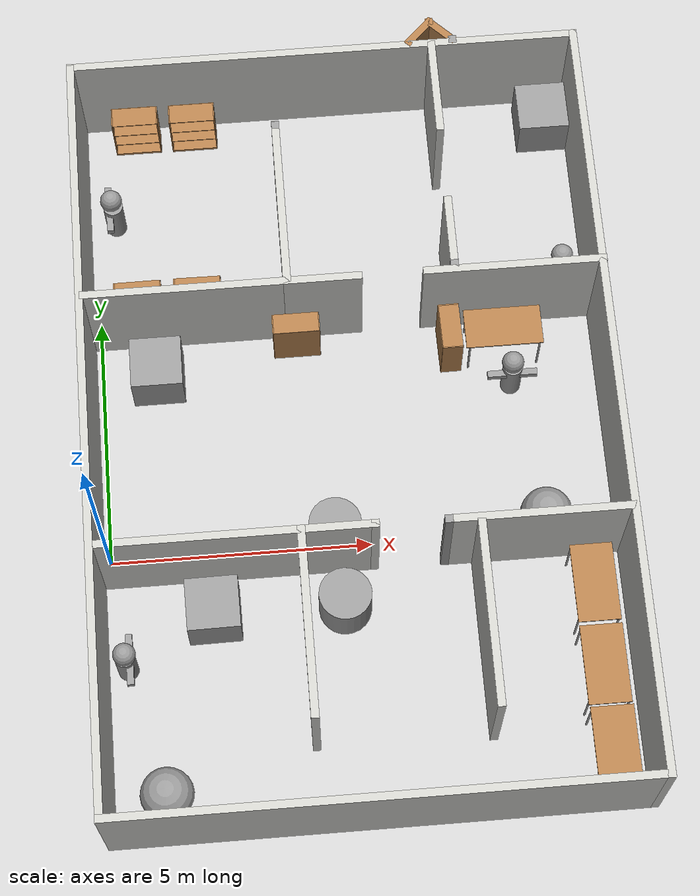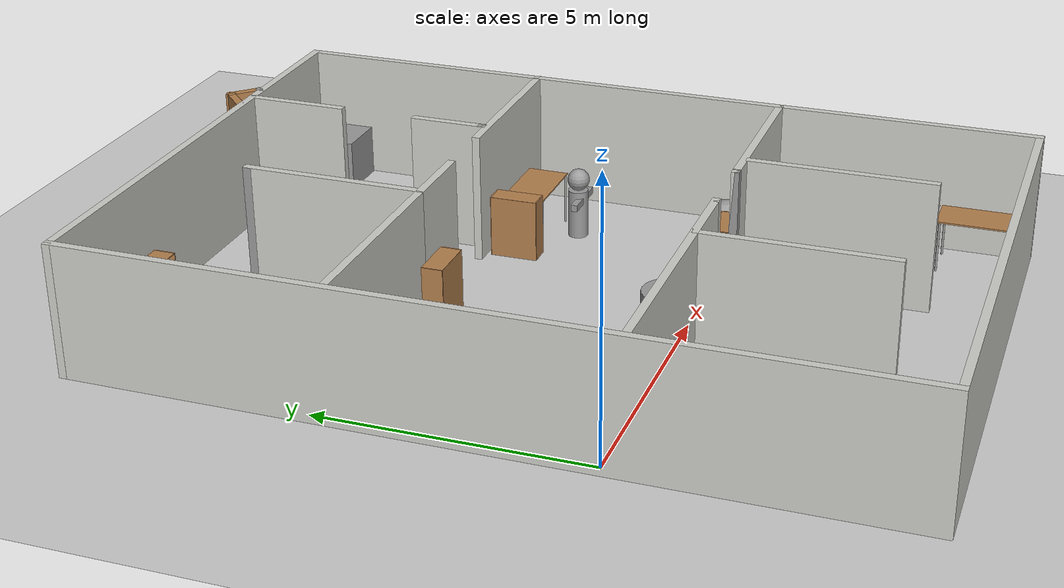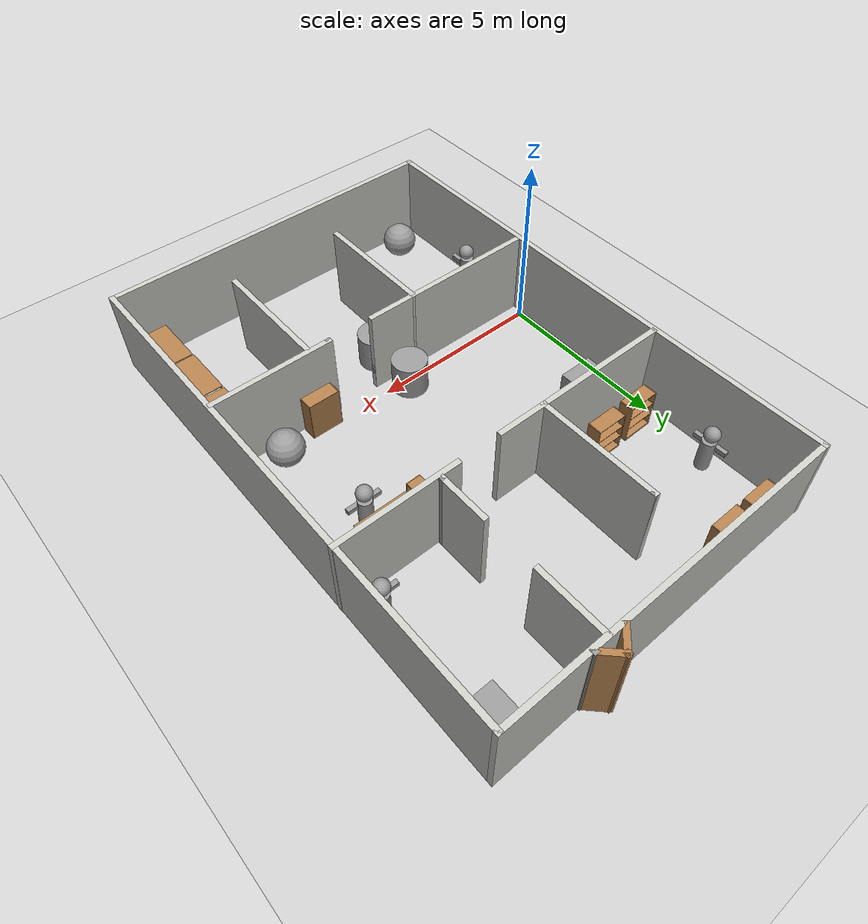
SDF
<sdf version="1.7">
 <world name="default">
  <light name="sun" type="directional">
   <pose>0 0 10 0 -0 0</pose>
   <diffuse>0.8 0.8 0.8 1</diffuse>
   <specular>0.2 0.2 0.2 1</specular>
   <attenuation>
    <range>1000</range>
    <constant>0.9</constant>
    <linear>0.01</linear>
    <quadratic>0.001</quadratic>
   </attenuation>
   <direction>-0.5 0.1 -0.9</direction>
   <spot><inner_angle>0</inner_angle><outer_angle>0</outer_angle><falloff>0</falloff></spot>
  </light>
  <model name="ground_plane">
   <static>1</static>
   <link name="link">
    <collision name="collision">
     <geometry><plane><normal>0 0 1</normal><size>100 100</size></plane></geometry>
     <surface><friction><ode><mu>100</mu><mu2>50</mu2></ode></friction></surface>
    </collision>
    <visual name="visual">
     <cast_shadows>0</cast_shadows>
     <geometry><plane><normal>0 0 1</normal><size>100 100</size></plane></geometry>
     <material>
      <script><uri>file://media/materials/scripts/gazebo.material</uri><name>Gazebo/Grey</name></script>
     </material>
    </visual>
   </link>
  </model>
  <gravity>0 0 -9.8</gravity>
  <magnetic_field>6e-06 2.3e-05 -4.2e-05</magnetic_field>
  <atmosphere type="adiabatic"/>
  <physics type="ode">
   <max_step_size>0.001</max_step_size>
   <real_time_factor>1</real_time_factor>
   <real_time_update_rate>1000</real_time_update_rate>
  </physics>
  <scene><ambient>0.4 0.4 0.4 1</ambient><background>0.7 0.7 0.7 1</background><shadows>1</shadows></scene>
  <spherical_coordinates>
   <surface_model>EARTH_WGS84</surface_model>
   <latitude_deg>0</latitude_deg>
   <longitude_deg>0</longitude_deg>
   <elevation>0</elevation>
   <heading_deg>0</heading_deg>
  </spherical_coordinates>
  <model name="School">
   <link name="Wall_17">
    <pose>0.254991 -4.96898 0 0 -0 0</pose>
    <visual name="Wall_17_Visual">
     <pose>0 0 1.25 0 -0 0</pose>
     <geometry><box><size>15 0.15 2.5</size></box></geometry>
     <material>
      <script><uri>file://media/materials/scripts/gazebo.material</uri><name>Gazebo/CeilingTiled</name></script>
      <ambient>1 1 1 1</ambient>
      <shader type="pixel"/>
     </material>
     <meta><layer>0</layer></meta>
    </visual>
    <collision name="Wall_17_Collision">
     <pose>0 0 1.25 0 -0 0</pose>
     <geometry><box><size>15 0.15 2.5</size></box></geometry>
     <surface>
      <friction>
       <ode><mu>1</mu><mu2>1</mu2><fdir1>0 0 0</fdir1><slip1>0</slip1><slip2>0</slip2></ode>
       <torsional>
        <coefficient>1</coefficient>
        <patch_radius>0</patch_radius>
        <surface_radius>0</surface_radius>
        <use_patch_radius>1</use_patch_radius>
        <ode><slip>0</slip></ode>
       </torsional>
      </friction>
      <bounce><restitution_coefficient>0</restitution_coefficient><threshold>1e+06</threshold></bounce>
      <contact>
       <collide_without_contact>0</collide_without_contact>
       <collide_without_contact_bitmask>1</collide_without_contact_bitmask>
       <collide_bitmask>1</collide_bitmask>
       <ode>
        <soft_cfm>0</soft_cfm>
        <soft_erp>0.2</soft_erp>
        <kp>1e+13</kp>
        <kd>1</kd>
        <max_vel>0.01</max_vel>
        <min_depth>0</min_depth>
       </ode>
       <bullet>
        <split_impulse>1</split_impulse>
        <split_impulse_penetration_threshold>-0.01</split_impulse_penetration_threshold>
        <soft_cfm>0</soft_cfm>
        <soft_erp>0.2</soft_erp>
        <kp>1e+13</kp>
        <kd>1</kd>
       </bullet>
      </contact>
     </surface>
    </collision>
   </link>
   <link name="Wall_19">
    <pose>7.67999 -0.04398 0 0 -0 1.5708</pose>
    <visual name="Wall_19_Visual">
     <pose>0 0 1.25 0 -0 0</pose>
     <geometry><box><size>10 0.15 2.5</size></box></geometry>
     <material>
      <script><uri>file://media/materials/scripts/gazebo.material</uri><name>Gazebo/CeilingTiled</name></script>
      <ambient>1 1 1 1</ambient>
      <shader type="pixel"/>
     </material>
     <meta><layer>0</layer></meta>
    </visual>
    <collision name="Wall_19_Collision">
     <pose>0 0 1.25 0 -0 0</pose>
     <geometry><box><size>10 0.15 2.5</size></box></geometry>
     <surface>
      <friction>
       <ode><mu>1</mu><mu2>1</mu2><fdir1>0 0 0</fdir1><slip1>0</slip1><slip2>0</slip2></ode>
       <torsional>
        <coefficient>1</coefficient>
        <patch_radius>0</patch_radius>
        <surface_radius>0</surface_radius>
        <use_patch_radius>1</use_patch_radius>
        <ode><slip>0</slip></ode>
       </torsional>
      </friction>
      <bounce><restitution_coefficient>0</restitution_coefficient><threshold>1e+06</threshold></bounce>
      <contact>
       <collide_without_contact>0</collide_without_contact>
       <collide_without_contact_bitmask>1</collide_without_contact_bitmask>
       <collide_bitmask>1</collide_bitmask>
       <ode>
        <soft_cfm>0</soft_cfm>
        <soft_erp>0.2</soft_erp>
        <kp>1e+13</kp>
        <kd>1</kd>
        <max_vel>0.01</max_vel>
        <min_depth>0</min_depth>
       </ode>
       <bullet>
        <split_impulse>1</split_impulse>
        <split_impulse_penetration_threshold>-0.01</split_impulse_penetration_threshold>
        <soft_cfm>0</soft_cfm>
        <soft_erp>0.2</soft_erp>
        <kp>1e+13</kp>
        <kd>1</kd>
       </bullet>
      </contact>
     </surface>
    </collision>
   </link>
   <link name="Wall_21">
    <pose>2.71343 -2.97254 0 0 -0 1.56975</pose>
    <visual name="Wall_21_Visual">
     <pose>0 0 1.25 0 -0 0</pose>
     <geometry><box><size>3.84171 0.15 2.5</size></box></geometry>
     <material>
      <script><uri>file://media/materials/scripts/gazebo.material</uri><name>Gazebo/CeilingTiled</name></script>
      <ambient>1 1 1 1</ambient>
      <shader type="pixel"/>
     </material>
     <meta><layer>0</layer></meta>
    </visual>
    <collision name="Wall_21_Collision">
     <pose>0 0 1.25 0 -0 0</pose>
     <geometry><box><size>3.84171 0.15 2.5</size></box></geometry>
     <surface>
      <friction>
       <ode><mu>1</mu><mu2>1</mu2><fdir1>0 0 0</fdir1><slip1>0</slip1><slip2>0</slip2></ode>
       <torsional>
        <coefficient>1</coefficient>
        <patch_radius>0</patch_radius>
        <surface_radius>0</surface_radius>
        <use_patch_radius>1</use_patch_radius>
        <ode><slip>0</slip></ode>
       </torsional>
      </friction>
      <bounce><restitution_coefficient>0</restitution_coefficient><threshold>1e+06</threshold></bounce>
      <contact>
       <collide_without_contact>0</collide_without_contact>
       <collide_without_contact_bitmask>1</collide_without_contact_bitmask>
       <collide_bitmask>1</collide_bitmask>
       <ode>
        <soft_cfm>0</soft_cfm>
        <soft_erp>0.2</soft_erp>
        <kp>1e+13</kp>
        <kd>1</kd>
        <max_vel>0.01</max_vel>
        <min_depth>0</min_depth>
       </ode>
       <bullet>
        <split_impulse>1</split_impulse>
        <split_impulse_penetration_threshold>-0.01</split_impulse_penetration_threshold>
        <soft_cfm>0</soft_cfm>
        <soft_erp>0.2</soft_erp>
        <kp>1e+13</kp>
        <kd>1</kd>
       </bullet>
      </contact>
     </surface>
    </collision>
   </link>
   <link name="Wall_25">
    <pose>-7.17001 -0.00448 0 0 -0 1.5708</pose>
    <visual name="Wall_25_Visual">
     <pose>0 0 1.25 0 -0 0</pose>
     <geometry><box><size>10.0791 0.15 2.5</size></box></geometry>
     <material>
      <script><uri>file://media/materials/scripts/gazebo.material</uri><name>Gazebo/CeilingTiled</name></script>
      <ambient>1 1 1 1</ambient>
      <shader type="pixel"/>
     </material>
     <meta><layer>0</layer></meta>
    </visual>
    <collision name="Wall_25_Collision">
     <pose>0 0 1.25 0 -0 0</pose>
     <geometry><box><size>10.0791 0.15 2.5</size></box></geometry>
     <surface>
      <friction>
       <ode><mu>1</mu><mu2>1</mu2><fdir1>0 0 0</fdir1><slip1>0</slip1><slip2>0</slip2></ode>
       <torsional>
        <coefficient>1</coefficient>
        <patch_radius>0</patch_radius>
        <surface_radius>0</surface_radius>
        <use_patch_radius>1</use_patch_radius>
        <ode><slip>0</slip></ode>
       </torsional>
      </friction>
      <bounce><restitution_coefficient>0</restitution_coefficient><threshold>1e+06</threshold></bounce>
      <contact>
       <collide_without_contact>0</collide_without_contact>
       <collide_without_contact_bitmask>1</collide_without_contact_bitmask>
       <collide_bitmask>1</collide_bitmask>
       <ode>
        <soft_cfm>0</soft_cfm>
        <soft_erp>0.2</soft_erp>
        <kp>1e+13</kp>
        <kd>1</kd>
        <max_vel>0.01</max_vel>
        <min_depth>0</min_depth>
       </ode>
       <bullet>
        <split_impulse>1</split_impulse>
        <split_impulse_penetration_threshold>-0.01</split_impulse_penetration_threshold>
        <soft_cfm>0</soft_cfm>
        <soft_erp>0.2</soft_erp>
        <kp>1e+13</kp>
        <kd>1</kd>
       </bullet>
      </contact>
     </surface>
    </collision>
   </link>
   <link name="Wall_27">
    <pose>-2.23801 -2.96498 0 0 -0 1.5708</pose>
    <visual name="Wall_27_Visual">
     <pose>0 0 1.25 0 -0 0</pose>
     <geometry><box><size>4 0.15 2.5</size></box></geometry>
     <material>
      <script><uri>file://media/materials/scripts/gazebo.material</uri><name>Gazebo/CeilingTiled</name></script>
      <ambient>1 1 1 1</ambient>
      <shader type="pixel"/>
     </material>
     <meta><layer>0</layer></meta>
    </visual>
    <collision name="Wall_27_Collision">
     <pose>0 0 1.25 0 -0 0</pose>
     <geometry><box><size>4 0.15 2.5</size></box></geometry>
     <surface>
      <friction>
       <ode><mu>1</mu><mu2>1</mu2><fdir1>0 0 0</fdir1><slip1>0</slip1><slip2>0</slip2></ode>
       <torsional>
        <coefficient>1</coefficient>
        <patch_radius>0</patch_radius>
        <surface_radius>0</surface_radius>
        <use_patch_radius>1</use_patch_radius>
        <ode><slip>0</slip></ode>
       </torsional>
      </friction>
      <bounce><restitution_coefficient>0</restitution_coefficient><threshold>1e+06</threshold></bounce>
      <contact>
       <collide_without_contact>0</collide_without_contact>
       <collide_without_contact_bitmask>1</collide_without_contact_bitmask>
       <collide_bitmask>1</collide_bitmask>
       <ode>
        <soft_cfm>0</soft_cfm>
        <soft_erp>0.2</soft_erp>
        <kp>1e+13</kp>
        <kd>1</kd>
        <max_vel>0.01</max_vel>
        <min_depth>0</min_depth>
       </ode>
       <bullet>
        <split_impulse>1</split_impulse>
        <split_impulse_penetration_threshold>-0.01</split_impulse_penetration_threshold>
        <soft_cfm>0</soft_cfm>
        <soft_erp>0.2</soft_erp>
        <kp>1e+13</kp>
        <kd>1</kd>
       </bullet>
      </contact>
     </surface>
    </collision>
   </link>
   <link name="Wall_29">
    <pose>-3.91301 -1.03998 0 0 -0 3.14159</pose>
    <visual name="Wall_29_Visual">
     <pose>0 0 1.25 0 -0 0</pose>
     <geometry><box><size>3.5 0.15 2.5</size></box></geometry>
     <material>
      <script><uri>file://media/materials/scripts/gazebo.material</uri><name>Gazebo/CeilingTiled</name></script>
      <ambient>1 1 1 1</ambient>
      <shader type="pixel"/>
     </material>
     <meta><layer>0</layer></meta>
    </visual>
    <collision name="Wall_29_Collision">
     <pose>0 0 1.25 0 -0 0</pose>
     <geometry><box><size>3.5 0.15 2.5</size></box></geometry>
     <surface>
      <friction>
       <ode><mu>1</mu><mu2>1</mu2><fdir1>0 0 0</fdir1><slip1>0</slip1><slip2>0</slip2></ode>
       <torsional>
        <coefficient>1</coefficient>
        <patch_radius>0</patch_radius>
        <surface_radius>0</surface_radius>
        <use_patch_radius>1</use_patch_radius>
        <ode><slip>0</slip></ode>
       </torsional>
      </friction>
      <bounce><restitution_coefficient>0</restitution_coefficient><threshold>1e+06</threshold></bounce>
      <contact>
       <collide_without_contact>0</collide_without_contact>
       <collide_without_contact_bitmask>1</collide_without_contact_bitmask>
       <collide_bitmask>1</collide_bitmask>
       <ode>
        <soft_cfm>0</soft_cfm>
        <soft_erp>0.2</soft_erp>
        <kp>1e+13</kp>
        <kd>1</kd>
        <max_vel>0.01</max_vel>
        <min_depth>0</min_depth>
       </ode>
       <bullet>
        <split_impulse>1</split_impulse>
        <split_impulse_penetration_threshold>-0.01</split_impulse_penetration_threshold>
        <soft_cfm>0</soft_cfm>
        <soft_erp>0.2</soft_erp>
        <kp>1e+13</kp>
        <kd>1</kd>
       </bullet>
      </contact>
     </surface>
    </collision>
   </link>
   <link name="Wall_30">
    <pose>-5.58301 -1.03998 0 0 -0 0</pose>
    <visual name="Wall_30_Visual">
     <pose>0 0 1.25 0 -0 0</pose>
     <geometry><box><size>0.16 0.15 2.5</size></box></geometry>
     <material>
      <script><uri>file://media/materials/scripts/gazebo.material</uri><name>Gazebo/Grey</name></script>
      <ambient>1 1 1 1</ambient>
      <shader type="pixel"/>
     </material>
     <meta><layer>0</layer></meta>
    </visual>
    <collision name="Wall_30_Collision">
     <pose>0 0 1.25 0 -0 0</pose>
     <geometry><box><size>0.16 0.15 2.5</size></box></geometry>
     <surface>
      <friction>
       <ode><mu>1</mu><mu2>1</mu2><fdir1>0 0 0</fdir1><slip1>0</slip1><slip2>0</slip2></ode>
       <torsional>
        <coefficient>1</coefficient>
        <patch_radius>0</patch_radius>
        <surface_radius>0</surface_radius>
        <use_patch_radius>1</use_patch_radius>
        <ode><slip>0</slip></ode>
       </torsional>
      </friction>
      <bounce><restitution_coefficient>0</restitution_coefficient><threshold>1e+06</threshold></bounce>
      <contact>
       <collide_without_contact>0</collide_without_contact>
       <collide_without_contact_bitmask>1</collide_without_contact_bitmask>
       <collide_bitmask>1</collide_bitmask>
       <ode>
        <soft_cfm>0</soft_cfm>
        <soft_erp>0.2</soft_erp>
        <kp>1e+13</kp>
        <kd>1</kd>
        <max_vel>0.01</max_vel>
        <min_depth>0</min_depth>
       </ode>
       <bullet>
        <split_impulse>1</split_impulse>
        <split_impulse_penetration_threshold>-0.01</split_impulse_penetration_threshold>
        <soft_cfm>0</soft_cfm>
        <soft_erp>0.2</soft_erp>
        <kp>1e+13</kp>
        <kd>1</kd>
       </bullet>
      </contact>
     </surface>
    </collision>
   </link>
   <link name="Wall_32">
    <pose>4.42767 -1.12668 0 0 -0 0</pose>
    <visual name="Wall_32_Visual">
     <pose>0 0 1.25 0 -0 0</pose>
     <geometry><box><size>3.57462 0.15 2.5</size></box></geometry>
     <material>
      <script><uri>file://media/materials/scripts/gazebo.material</uri><name>Gazebo/CeilingTiled</name></script>
      <ambient>1 1 1 1</ambient>
      <shader type="pixel"/>
     </material>
     <meta><layer>0</layer></meta>
    </visual>
    <collision name="Wall_32_Collision">
     <pose>0 0 1.25 0 -0 0</pose>
     <geometry><box><size>3.57462 0.15 2.5</size></box></geometry>
     <surface>
      <friction>
       <ode><mu>1</mu><mu2>1</mu2><fdir1>0 0 0</fdir1><slip1>0</slip1><slip2>0</slip2></ode>
       <torsional>
        <coefficient>1</coefficient>
        <patch_radius>0</patch_radius>
        <surface_radius>0</surface_radius>
        <use_patch_radius>1</use_patch_radius>
        <ode><slip>0</slip></ode>
       </torsional>
      </friction>
      <bounce><restitution_coefficient>0</restitution_coefficient><threshold>1e+06</threshold></bounce>
      <contact>
       <collide_without_contact>0</collide_without_contact>
       <collide_without_contact_bitmask>1</collide_without_contact_bitmask>
       <collide_bitmask>1</collide_bitmask>
       <ode>
        <soft_cfm>0</soft_cfm>
        <soft_erp>0.2</soft_erp>
        <kp>1e+13</kp>
        <kd>1</kd>
        <max_vel>0.01</max_vel>
        <min_depth>0</min_depth>
       </ode>
       <bullet>
        <split_impulse>1</split_impulse>
        <split_impulse_penetration_threshold>-0.01</split_impulse_penetration_threshold>
        <soft_cfm>0</soft_cfm>
        <soft_erp>0.2</soft_erp>
        <kp>1e+13</kp>
        <kd>1</kd>
       </bullet>
      </contact>
     </surface>
    </collision>
   </link>
   <link name="Wall_36">
    <pose>0.254991 4.95997 0 0 0 -7e-06</pose>
    <visual name="Wall_36_Visual">
     <pose>0 0 1.25 0 -0 0</pose>
     <geometry><box><size>15 0.15 2.5</size></box></geometry>
     <material>
      <script><uri>file://media/materials/scripts/gazebo.material</uri><name>Gazebo/CeilingTiled</name></script>
      <ambient>1 1 1 1</ambient>
      <shader type="pixel"/>
     </material>
     <meta><layer>0</layer></meta>
    </visual>
    <collision name="Wall_36_Collision">
     <pose>0 0 1.25 0 -0 0</pose>
     <geometry><box><size>15 0.15 2.5</size></box></geometry>
     <surface>
      <friction>
       <ode><mu>1</mu><mu2>1</mu2><fdir1>0 0 0</fdir1><slip1>0</slip1><slip2>0</slip2></ode>
       <torsional>
        <coefficient>1</coefficient>
        <patch_radius>0</patch_radius>
        <surface_radius>0</surface_radius>
        <use_patch_radius>1</use_patch_radius>
        <ode><slip>0</slip></ode>
       </torsional>
      </friction>
      <bounce><restitution_coefficient>0</restitution_coefficient><threshold>1e+06</threshold></bounce>
      <contact>
       <collide_without_contact>0</collide_without_contact>
       <collide_without_contact_bitmask>1</collide_without_contact_bitmask>
       <collide_bitmask>1</collide_bitmask>
       <ode>
        <soft_cfm>0</soft_cfm>
        <soft_erp>0.2</soft_erp>
        <kp>1e+13</kp>
        <kd>1</kd>
        <max_vel>0.01</max_vel>
        <min_depth>0</min_depth>
       </ode>
       <bullet>
        <split_impulse>1</split_impulse>
        <split_impulse_penetration_threshold>-0.01</split_impulse_penetration_threshold>
        <soft_cfm>0</soft_cfm>
        <soft_erp>0.2</soft_erp>
        <kp>1e+13</kp>
        <kd>1</kd>
       </bullet>
      </contact>
     </surface>
    </collision>
   </link>
   <link name="Wall_39">
    <pose>-2.23801 -0.36498 0 0 -0 1.5708</pose>
    <visual name="Wall_39_Visual">
     <pose>0 0 1.25 0 -0 0</pose>
     <geometry><box><size>1.5 0.15 2.5</size></box></geometry>
     <material>
      <script><uri>file://media/materials/scripts/gazebo.material</uri><name>Gazebo/CeilingTiled</name></script>
      <ambient>1 1 1 1</ambient>
      <shader type="pixel"/>
     </material>
     <meta><layer>0</layer></meta>
    </visual>
    <collision name="Wall_39_Collision">
     <pose>0 0 1.25 0 -0 0</pose>
     <geometry><box><size>1.5 0.15 2.5</size></box></geometry>
     <surface>
      <friction>
       <ode><mu>1</mu><mu2>1</mu2><fdir1>0 0 0</fdir1><slip1>0</slip1><slip2>0</slip2></ode>
       <torsional>
        <coefficient>1</coefficient>
        <patch_radius>0</patch_radius>
        <surface_radius>0</surface_radius>
        <use_patch_radius>1</use_patch_radius>
        <ode><slip>0</slip></ode>
       </torsional>
      </friction>
      <bounce><restitution_coefficient>0</restitution_coefficient><threshold>1e+06</threshold></bounce>
      <contact>
       <collide_without_contact>0</collide_without_contact>
       <collide_without_contact_bitmask>1</collide_without_contact_bitmask>
       <collide_bitmask>1</collide_bitmask>
       <ode>
        <soft_cfm>0</soft_cfm>
        <soft_erp>0.2</soft_erp>
        <kp>1e+13</kp>
        <kd>1</kd>
        <max_vel>0.01</max_vel>
        <min_depth>0</min_depth>
       </ode>
       <bullet>
        <split_impulse>1</split_impulse>
        <split_impulse_penetration_threshold>-0.01</split_impulse_penetration_threshold>
        <soft_cfm>0</soft_cfm>
        <soft_erp>0.2</soft_erp>
        <kp>1e+13</kp>
        <kd>1</kd>
       </bullet>
      </contact>
     </surface>
    </collision>
   </link>
   <link name="Wall_41">
    <pose>-2.23801 3.29402 0 0 0 -1.5708</pose>
    <visual name="Wall_41_Visual">
     <pose>0 0 1.25 0 -0 0</pose>
     <geometry><box><size>3.5 0.15 2.5</size></box></geometry>
     <material>
      <script><uri>file://media/materials/scripts/gazebo.material</uri><name>Gazebo/CeilingTiled</name></script>
      <ambient>1 1 1 1</ambient>
      <shader type="pixel"/>
     </material>
     <meta><layer>0</layer></meta>
    </visual>
    <collision name="Wall_41_Collision">
     <pose>0 0 1.25 0 -0 0</pose>
     <geometry><box><size>3.5 0.15 2.5</size></box></geometry>
     <surface>
      <friction>
       <ode><mu>1</mu><mu2>1</mu2><fdir1>0 0 0</fdir1><slip1>0</slip1><slip2>0</slip2></ode>
       <torsional>
        <coefficient>1</coefficient>
        <patch_radius>0</patch_radius>
        <surface_radius>0</surface_radius>
        <use_patch_radius>1</use_patch_radius>
        <ode><slip>0</slip></ode>
       </torsional>
      </friction>
      <bounce><restitution_coefficient>0</restitution_coefficient><threshold>1e+06</threshold></bounce>
      <contact>
       <collide_without_contact>0</collide_without_contact>
       <collide_without_contact_bitmask>1</collide_without_contact_bitmask>
       <collide_bitmask>1</collide_bitmask>
       <ode>
        <soft_cfm>0</soft_cfm>
        <soft_erp>0.2</soft_erp>
        <kp>1e+13</kp>
        <kd>1</kd>
        <max_vel>0.01</max_vel>
        <min_depth>0</min_depth>
       </ode>
       <bullet>
        <split_impulse>1</split_impulse>
        <split_impulse_penetration_threshold>-0.01</split_impulse_penetration_threshold>
        <soft_cfm>0</soft_cfm>
        <soft_erp>0.2</soft_erp>
        <kp>1e+13</kp>
        <kd>1</kd>
       </bullet>
      </contact>
     </surface>
    </collision>
   </link>
   <link name="Wall_46">
    <pose>2.73299 3.23402 0 0 0 -1.5708</pose>
    <visual name="Wall_46_Visual">
     <pose>0 0 1.25 0 -0 0</pose>
     <geometry><box><size>3.5 0.15 2.5</size></box></geometry>
     <material>
      <script><uri>file://media/materials/scripts/gazebo.material</uri><name>Gazebo/CeilingTiled</name></script>
      <ambient>1 1 1 1</ambient>
      <shader type="pixel"/>
     </material>
     <meta><layer>0</layer></meta>
    </visual>
    <collision name="Wall_46_Collision">
     <pose>0 0 1.25 0 -0 0</pose>
     <geometry><box><size>3.5 0.15 2.5</size></box></geometry>
     <surface>
      <friction>
       <ode><mu>1</mu><mu2>1</mu2><fdir1>0 0 0</fdir1><slip1>0</slip1><slip2>0</slip2></ode>
       <torsional>
        <coefficient>1</coefficient>
        <patch_radius>0</patch_radius>
        <surface_radius>0</surface_radius>
        <use_patch_radius>1</use_patch_radius>
        <ode><slip>0</slip></ode>
       </torsional>
      </friction>
      <bounce><restitution_coefficient>0</restitution_coefficient><threshold>1e+06</threshold></bounce>
      <contact>
       <collide_without_contact>0</collide_without_contact>
       <collide_without_contact_bitmask>1</collide_without_contact_bitmask>
       <collide_bitmask>1</collide_bitmask>
       <ode>
        <soft_cfm>0</soft_cfm>
        <soft_erp>0.2</soft_erp>
        <kp>1e+13</kp>
        <kd>1</kd>
        <max_vel>0.01</max_vel>
        <min_depth>0</min_depth>
       </ode>
       <bullet>
        <split_impulse>1</split_impulse>
        <split_impulse_penetration_threshold>-0.01</split_impulse_penetration_threshold>
        <soft_cfm>0</soft_cfm>
        <soft_erp>0.2</soft_erp>
        <kp>1e+13</kp>
        <kd>1</kd>
       </bullet>
      </contact>
     </surface>
    </collision>
   </link>
   <link name="Wall_47">
    <pose>2.73299 1.55902 0 0 -0 0</pose>
    <visual name="Wall_47_Visual">
     <pose>0 0 1.25 0 -0 0</pose>
     <geometry><box><size>0.15 0.15 2.5</size></box></geometry>
     <material>
      <script><uri>file://media/materials/scripts/gazebo.material</uri><name>Gazebo/Grey</name></script>
      <ambient>1 1 1 1</ambient>
      <shader type="pixel"/>
     </material>
     <meta><layer>0</layer></meta>
    </visual>
    <collision name="Wall_47_Collision">
     <pose>0 0 1.25 0 -0 0</pose>
     <geometry><box><size>0.15 0.15 2.5</size></box></geometry>
     <surface>
      <friction>
       <ode><mu>1</mu><mu2>1</mu2><fdir1>0 0 0</fdir1><slip1>0</slip1><slip2>0</slip2></ode>
       <torsional>
        <coefficient>1</coefficient>
        <patch_radius>0</patch_radius>
        <surface_radius>0</surface_radius>
        <use_patch_radius>1</use_patch_radius>
        <ode><slip>0</slip></ode>
       </torsional>
      </friction>
      <bounce><restitution_coefficient>0</restitution_coefficient><threshold>1e+06</threshold></bounce>
      <contact>
       <collide_without_contact>0</collide_without_contact>
       <collide_without_contact_bitmask>1</collide_without_contact_bitmask>
       <collide_bitmask>1</collide_bitmask>
       <ode>
        <soft_cfm>0</soft_cfm>
        <soft_erp>0.2</soft_erp>
        <kp>1e+13</kp>
        <kd>1</kd>
        <max_vel>0.01</max_vel>
        <min_depth>0</min_depth>
       </ode>
       <bullet>
        <split_impulse>1</split_impulse>
        <split_impulse_penetration_threshold>-0.01</split_impulse_penetration_threshold>
        <soft_cfm>0</soft_cfm>
        <soft_erp>0.2</soft_erp>
        <kp>1e+13</kp>
        <kd>1</kd>
       </bullet>
      </contact>
     </surface>
    </collision>
   </link>
   <link name="Wall_49">
    <pose>2.71536 -0.45168 0 0 -0 1.5708</pose>
    <visual name="Wall_49_Visual">
     <pose>0 0 1.25 0 -0 0</pose>
     <geometry><box><size>1.5 0.15 2.5</size></box></geometry>
     <material>
      <script><uri>file://media/materials/scripts/gazebo.material</uri><name>Gazebo/CeilingTiled</name></script>
      <ambient>1 1 1 1</ambient>
      <shader type="pixel"/>
     </material>
     <meta><layer>0</layer></meta>
    </visual>
    <collision name="Wall_49_Collision">
     <pose>0 0 1.25 0 -0 0</pose>
     <geometry><box><size>1.5 0.15 2.5</size></box></geometry>
     <surface>
      <friction>
       <ode><mu>1</mu><mu2>1</mu2><fdir1>0 0 0</fdir1><slip1>0</slip1><slip2>0</slip2></ode>
       <torsional>
        <coefficient>1</coefficient>
        <patch_radius>0</patch_radius>
        <surface_radius>0</surface_radius>
        <use_patch_radius>1</use_patch_radius>
        <ode><slip>0</slip></ode>
       </torsional>
      </friction>
      <bounce><restitution_coefficient>0</restitution_coefficient><threshold>1e+06</threshold></bounce>
      <contact>
       <collide_without_contact>0</collide_without_contact>
       <collide_without_contact_bitmask>1</collide_without_contact_bitmask>
       <collide_bitmask>1</collide_bitmask>
       <ode>
        <soft_cfm>0</soft_cfm>
        <soft_erp>0.2</soft_erp>
        <kp>1e+13</kp>
        <kd>1</kd>
        <max_vel>0.01</max_vel>
        <min_depth>0</min_depth>
       </ode>
       <bullet>
        <split_impulse>1</split_impulse>
        <split_impulse_penetration_threshold>-0.01</split_impulse_penetration_threshold>
        <soft_cfm>0</soft_cfm>
        <soft_erp>0.2</soft_erp>
        <kp>1e+13</kp>
        <kd>1</kd>
       </bullet>
      </contact>
     </surface>
    </collision>
   </link>
   <link name="Wall_50">
    <pose>2.71536 0.22332 0 0 -0 0</pose>
    <visual name="Wall_50_Visual">
     <pose>0 0 1.25 0 -0 0</pose>
     <geometry><box><size>0.15 0.15 2.5</size></box></geometry>
     <material>
      <script><uri>file://media/materials/scripts/gazebo.material</uri><name>Gazebo/CeilingTiled</name></script>
      <ambient>1 1 1 1</ambient>
      <shader type="pixel"/>
     </material>
     <meta><layer>0</layer></meta>
    </visual>
    <collision name="Wall_50_Collision">
     <pose>0 0 1.25 0 -0 0</pose>
     <geometry><box><size>0.15 0.15 2.5</size></box></geometry>
     <surface>
      <friction>
       <ode><mu>1</mu><mu2>1</mu2><fdir1>0 0 0</fdir1><slip1>0</slip1><slip2>0</slip2></ode>
       <torsional>
        <coefficient>1</coefficient>
        <patch_radius>0</patch_radius>
        <surface_radius>0</surface_radius>
        <use_patch_radius>1</use_patch_radius>
        <ode><slip>0</slip></ode>
       </torsional>
      </friction>
      <bounce><restitution_coefficient>0</restitution_coefficient><threshold>1e+06</threshold></bounce>
      <contact>
       <collide_without_contact>0</collide_without_contact>
       <collide_without_contact_bitmask>1</collide_without_contact_bitmask>
       <collide_bitmask>1</collide_bitmask>
       <ode>
        <soft_cfm>0</soft_cfm>
        <soft_erp>0.2</soft_erp>
        <kp>1e+13</kp>
        <kd>1</kd>
        <max_vel>0.01</max_vel>
        <min_depth>0</min_depth>
       </ode>
       <bullet>
        <split_impulse>1</split_impulse>
        <split_impulse_penetration_threshold>-0.01</split_impulse_penetration_threshold>
        <soft_cfm>0</soft_cfm>
        <soft_erp>0.2</soft_erp>
        <kp>1e+13</kp>
        <kd>1</kd>
       </bullet>
      </contact>
     </surface>
    </collision>
   </link>
   <link name="Wall_53">
    <pose>-7.64893 2.15204 0 0 -0 0</pose>
    <visual name="Wall_53_Visual">
     <pose>0 0 1.25 0 -0 0</pose>
     <geometry><box><size>0.15 0.15 2.5</size></box></geometry>
     <material>
      <script><uri>file://media/materials/scripts/gazebo.material</uri><name>Gazebo/Wood</name></script>
      <ambient>1 1 1 1</ambient>
      <shader type="pixel"/>
     </material>
     <meta><layer>0</layer></meta>
    </visual>
    <collision name="Wall_53_Collision">
     <pose>0 0 1.25 0 -0 0</pose>
     <geometry><box><size>0.15 0.15 2.5</size></box></geometry>
     <surface>
      <friction>
       <ode><mu>1</mu><mu2>1</mu2><fdir1>0 0 0</fdir1><slip1>0</slip1><slip2>0</slip2></ode>
       <torsional>
        <coefficient>1</coefficient>
        <patch_radius>0</patch_radius>
        <surface_radius>0</surface_radius>
        <use_patch_radius>1</use_patch_radius>
        <ode><slip>0</slip></ode>
       </torsional>
      </friction>
      <bounce><restitution_coefficient>0</restitution_coefficient><threshold>1e+06</threshold></bounce>
      <contact>
       <collide_without_contact>0</collide_without_contact>
       <collide_without_contact_bitmask>1</collide_without_contact_bitmask>
       <collide_bitmask>1</collide_bitmask>
       <ode>
        <soft_cfm>0</soft_cfm>
        <soft_erp>0.2</soft_erp>
        <kp>1e+13</kp>
        <kd>1</kd>
        <max_vel>0.01</max_vel>
        <min_depth>0</min_depth>
       </ode>
       <bullet>
        <split_impulse>1</split_impulse>
        <split_impulse_penetration_threshold>-0.01</split_impulse_penetration_threshold>
        <soft_cfm>0</soft_cfm>
        <soft_erp>0.2</soft_erp>
        <kp>1e+13</kp>
        <kd>1</kd>
       </bullet>
      </contact>
     </surface>
    </collision>
   </link>
   <link name="Wall_55">
    <pose>-6.21671 2.15116 0 0 -0 0</pose>
    <visual name="Wall_55_Visual">
     <pose>0 0 1.25 0 -0 0</pose>
     <geometry><box><size>2 0.15 2.5</size></box></geometry>
     <material>
      <script><uri>file://media/materials/scripts/gazebo.material</uri><name>Gazebo/CeilingTiled</name></script>
      <ambient>1 1 1 1</ambient>
      <shader type="pixel"/>
     </material>
     <meta><layer>0</layer></meta>
    </visual>
    <collision name="Wall_55_Collision">
     <pose>0 0 1.25 0 -0 0</pose>
     <geometry><box><size>2 0.15 2.5</size></box></geometry>
     <surface>
      <friction>
       <ode><mu>1</mu><mu2>1</mu2><fdir1>0 0 0</fdir1><slip1>0</slip1><slip2>0</slip2></ode>
       <torsional>
        <coefficient>1</coefficient>
        <patch_radius>0</patch_radius>
        <surface_radius>0</surface_radius>
        <use_patch_radius>1</use_patch_radius>
        <ode><slip>0</slip></ode>
       </torsional>
      </friction>
      <bounce><restitution_coefficient>0</restitution_coefficient><threshold>1e+06</threshold></bounce>
      <contact>
       <collide_without_contact>0</collide_without_contact>
       <collide_without_contact_bitmask>1</collide_without_contact_bitmask>
       <collide_bitmask>1</collide_bitmask>
       <ode>
        <soft_cfm>0</soft_cfm>
        <soft_erp>0.2</soft_erp>
        <kp>1e+13</kp>
        <kd>1</kd>
        <max_vel>0.01</max_vel>
        <min_depth>0</min_depth>
       </ode>
       <bullet>
        <split_impulse>1</split_impulse>
        <split_impulse_penetration_threshold>-0.01</split_impulse_penetration_threshold>
        <soft_cfm>0</soft_cfm>
        <soft_erp>0.2</soft_erp>
        <kp>1e+13</kp>
        <kd>1</kd>
       </bullet>
      </contact>
     </surface>
    </collision>
   </link>
   <link name="Wall_57">
    <pose>-3.02201 2.15102 0 0 -0 0</pose>
    <visual name="Wall_57_Visual">
     <pose>0 0 1.25 0 -0 0</pose>
     <geometry><box><size>1.5 0.15 2.5</size></box></geometry>
     <material>
      <script><uri>file://media/materials/scripts/gazebo.material</uri><name>Gazebo/CeilingTiled</name></script>
      <ambient>1 1 1 1</ambient>
      <shader type="pixel"/>
     </material>
     <meta><layer>0</layer></meta>
    </visual>
    <collision name="Wall_57_Collision">
     <pose>0 0 1.25 0 -0 0</pose>
     <geometry><box><size>1.5 0.15 2.5</size></box></geometry>
     <surface>
      <friction>
       <ode><mu>1</mu><mu2>1</mu2><fdir1>0 0 0</fdir1><slip1>0</slip1><slip2>0</slip2></ode>
       <torsional>
        <coefficient>1</coefficient>
        <patch_radius>0</patch_radius>
        <surface_radius>0</surface_radius>
        <use_patch_radius>1</use_patch_radius>
        <ode><slip>0</slip></ode>
       </torsional>
      </friction>
      <bounce><restitution_coefficient>0</restitution_coefficient><threshold>1e+06</threshold></bounce>
      <contact>
       <collide_without_contact>0</collide_without_contact>
       <collide_without_contact_bitmask>1</collide_without_contact_bitmask>
       <collide_bitmask>1</collide_bitmask>
       <ode>
        <soft_cfm>0</soft_cfm>
        <soft_erp>0.2</soft_erp>
        <kp>1e+13</kp>
        <kd>1</kd>
        <max_vel>0.01</max_vel>
        <min_depth>0</min_depth>
       </ode>
       <bullet>
        <split_impulse>1</split_impulse>
        <split_impulse_penetration_threshold>-0.01</split_impulse_penetration_threshold>
        <soft_cfm>0</soft_cfm>
        <soft_erp>0.2</soft_erp>
        <kp>1e+13</kp>
        <kd>1</kd>
       </bullet>
      </contact>
     </surface>
    </collision>
   </link>
   <link name="Wall_58">
    <pose>-2.34701 2.15102 0 0 -0 0</pose>
    <visual name="Wall_58_Visual">
     <pose>0 0 1.25 0 -0 0</pose>
     <geometry><box><size>0.15 0.15 2.5</size></box></geometry>
     <material>
      <script><uri>file://media/materials/scripts/gazebo.material</uri><name>Gazebo/Grey</name></script>
      <ambient>1 1 1 1</ambient>
      <shader type="pixel"/>
     </material>
     <meta><layer>0</layer></meta>
    </visual>
    <collision name="Wall_58_Collision">
     <pose>0 0 1.25 0 -0 0</pose>
     <geometry><box><size>0.15 0.15 2.5</size></box></geometry>
     <surface>
      <friction>
       <ode><mu>1</mu><mu2>1</mu2><fdir1>0 0 0</fdir1><slip1>0</slip1><slip2>0</slip2></ode>
       <torsional>
        <coefficient>1</coefficient>
        <patch_radius>0</patch_radius>
        <surface_radius>0</surface_radius>
        <use_patch_radius>1</use_patch_radius>
        <ode><slip>0</slip></ode>
       </torsional>
      </friction>
      <bounce><restitution_coefficient>0</restitution_coefficient><threshold>1e+06</threshold></bounce>
      <contact>
       <collide_without_contact>0</collide_without_contact>
       <collide_without_contact_bitmask>1</collide_without_contact_bitmask>
       <collide_bitmask>1</collide_bitmask>
       <ode>
        <soft_cfm>0</soft_cfm>
        <soft_erp>0.2</soft_erp>
        <kp>1e+13</kp>
        <kd>1</kd>
        <max_vel>0.01</max_vel>
        <min_depth>0</min_depth>
       </ode>
       <bullet>
        <split_impulse>1</split_impulse>
        <split_impulse_penetration_threshold>-0.01</split_impulse_penetration_threshold>
        <soft_cfm>0</soft_cfm>
        <soft_erp>0.2</soft_erp>
        <kp>1e+13</kp>
        <kd>1</kd>
       </bullet>
      </contact>
     </surface>
    </collision>
   </link>
   <link name="Wall_61">
    <pose>4.51973 2.15102 0 0 -0 0</pose>
    <visual name="Wall_61_Visual">
     <pose>0 0 1.25 0 -0 0</pose>
     <geometry><box><size>3.5 0.15 2.5</size></box></geometry>
     <material>
      <script><uri>file://media/materials/scripts/gazebo.material</uri><name>Gazebo/CeilingTiled</name></script>
      <ambient>1 1 1 1</ambient>
      <shader type="pixel"/>
     </material>
     <meta><layer>0</layer></meta>
    </visual>
    <collision name="Wall_61_Collision">
     <pose>0 0 1.25 0 -0 0</pose>
     <geometry><box><size>3.5 0.15 2.5</size></box></geometry>
     <surface>
      <friction>
       <ode><mu>1</mu><mu2>1</mu2><fdir1>0 0 0</fdir1><slip1>0</slip1><slip2>0</slip2></ode>
       <torsional>
        <coefficient>1</coefficient>
        <patch_radius>0</patch_radius>
        <surface_radius>0</surface_radius>
        <use_patch_radius>1</use_patch_radius>
        <ode><slip>0</slip></ode>
       </torsional>
      </friction>
      <bounce><restitution_coefficient>0</restitution_coefficient><threshold>1e+06</threshold></bounce>
      <contact>
       <collide_without_contact>0</collide_without_contact>
       <collide_without_contact_bitmask>1</collide_without_contact_bitmask>
       <collide_bitmask>1</collide_bitmask>
       <ode>
        <soft_cfm>0</soft_cfm>
        <soft_erp>0.2</soft_erp>
        <kp>1e+13</kp>
        <kd>1</kd>
        <max_vel>0.01</max_vel>
        <min_depth>0</min_depth>
       </ode>
       <bullet>
        <split_impulse>1</split_impulse>
        <split_impulse_penetration_threshold>-0.01</split_impulse_penetration_threshold>
        <soft_cfm>0</soft_cfm>
        <soft_erp>0.2</soft_erp>
        <kp>1e+13</kp>
        <kd>1</kd>
       </bullet>
      </contact>
     </surface>
    </collision>
   </link>
   <link name="Wall_87">
    <pose>-7.43679 2.36417 0 0 -0 0.785398</pose>
    <visual name="Wall_87_Visual">
     <pose>0 0 1.25 0 -0 0</pose>
     <geometry><box><size>0.75 0.15 2.5</size></box></geometry>
     <material>
      <script><uri>file://media/materials/scripts/gazebo.material</uri><name>Gazebo/Wood</name></script>
      <ambient>1 1 1 1</ambient>
      <shader type="pixel"/>
     </material>
     <meta><layer>0</layer></meta>
    </visual>
    <collision name="Wall_87_Collision">
     <pose>0 0 1.25 0 -0 0</pose>
     <geometry><box><size>0.75 0.15 2.5</size></box></geometry>
     <surface>
      <friction>
       <ode><mu>1</mu><mu2>1</mu2><fdir1>0 0 0</fdir1><slip1>0</slip1><slip2>0</slip2></ode>
       <torsional>
        <coefficient>1</coefficient>
        <patch_radius>0</patch_radius>
        <surface_radius>0</surface_radius>
        <use_patch_radius>1</use_patch_radius>
        <ode><slip>0</slip></ode>
       </torsional>
      </friction>
      <bounce><restitution_coefficient>0</restitution_coefficient><threshold>1e+06</threshold></bounce>
      <contact>
       <collide_without_contact>0</collide_without_contact>
       <collide_without_contact_bitmask>1</collide_without_contact_bitmask>
       <collide_bitmask>1</collide_bitmask>
       <ode>
        <soft_cfm>0</soft_cfm>
        <soft_erp>0.2</soft_erp>
        <kp>1e+13</kp>
        <kd>1</kd>
        <max_vel>0.01</max_vel>
        <min_depth>0</min_depth>
       </ode>
       <bullet>
        <split_impulse>1</split_impulse>
        <split_impulse_penetration_threshold>-0.01</split_impulse_penetration_threshold>
        <soft_cfm>0</soft_cfm>
        <soft_erp>0.2</soft_erp>
        <kp>1e+13</kp>
        <kd>1</kd>
       </bullet>
      </contact>
     </surface>
    </collision>
   </link>
   <link name="Wall_88">
    <pose>-7.21966 2.5763 0 0 -0 0</pose>
    <visual name="Wall_88_Visual">
     <pose>0 0 1.25 0 -0 0</pose>
     <geometry><box><size>0.16 0.15 2.5</size></box></geometry>
     <material>
      <script><uri>file://media/materials/scripts/gazebo.material</uri><name>Gazebo/Grey</name></script>
      <ambient>1 1 1 1</ambient>
      <shader type="pixel"/>
     </material>
     <meta><layer>0</layer></meta>
    </visual>
    <collision name="Wall_88_Collision">
     <pose>0 0 1.25 0 -0 0</pose>
     <geometry><box><size>0.16 0.15 2.5</size></box></geometry>
     <surface>
      <friction>
       <ode><mu>1</mu><mu2>1</mu2><fdir1>0 0 0</fdir1><slip1>0</slip1><slip2>0</slip2></ode>
       <torsional>
        <coefficient>1</coefficient>
        <patch_radius>0</patch_radius>
        <surface_radius>0</surface_radius>
        <use_patch_radius>1</use_patch_radius>
        <ode><slip>0</slip></ode>
       </torsional>
      </friction>
      <bounce><restitution_coefficient>0</restitution_coefficient><threshold>1e+06</threshold></bounce>
      <contact>
       <collide_without_contact>0</collide_without_contact>
       <collide_without_contact_bitmask>1</collide_without_contact_bitmask>
       <collide_bitmask>1</collide_bitmask>
       <ode>
        <soft_cfm>0</soft_cfm>
        <soft_erp>0.2</soft_erp>
        <kp>1e+13</kp>
        <kd>1</kd>
        <max_vel>0.01</max_vel>
        <min_depth>0</min_depth>
       </ode>
       <bullet>
        <split_impulse>1</split_impulse>
        <split_impulse_penetration_threshold>-0.01</split_impulse_penetration_threshold>
        <soft_cfm>0</soft_cfm>
        <soft_erp>0.2</soft_erp>
        <kp>1e+13</kp>
        <kd>1</kd>
       </bullet>
      </contact>
     </surface>
    </collision>
   </link>
   <link name="Wall_90">
    <pose>-7.43679 1.9399 0 0 0 -0.785398</pose>
    <visual name="Wall_90_Visual">
     <pose>0 0 1.25 0 -0 0</pose>
     <geometry><box><size>0.75 0.15 2.5</size></box></geometry>
     <material>
      <script><uri>file://media/materials/scripts/gazebo.material</uri><name>Gazebo/Wood</name></script>
      <ambient>1 1 1 1</ambient>
      <shader type="pixel"/>
     </material>
     <meta><layer>0</layer></meta>
    </visual>
    <collision name="Wall_90_Collision">
     <pose>0 0 1.25 0 -0 0</pose>
     <geometry><box><size>0.75 0.15 2.5</size></box></geometry>
     <surface>
      <friction>
       <ode><mu>1</mu><mu2>1</mu2><fdir1>0 0 0</fdir1><slip1>0</slip1><slip2>0</slip2></ode>
       <torsional>
        <coefficient>1</coefficient>
        <patch_radius>0</patch_radius>
        <surface_radius>0</surface_radius>
        <use_patch_radius>1</use_patch_radius>
        <ode><slip>0</slip></ode>
       </torsional>
      </friction>
      <bounce><restitution_coefficient>0</restitution_coefficient><threshold>1e+06</threshold></bounce>
      <contact>
       <collide_without_contact>0</collide_without_contact>
       <collide_without_contact_bitmask>1</collide_without_contact_bitmask>
       <collide_bitmask>1</collide_bitmask>
       <ode>
        <soft_cfm>0</soft_cfm>
        <soft_erp>0.2</soft_erp>
        <kp>1e+13</kp>
        <kd>1</kd>
        <max_vel>0.01</max_vel>
        <min_depth>0</min_depth>
       </ode>
       <bullet>
        <split_impulse>1</split_impulse>
        <split_impulse_penetration_threshold>-0.01</split_impulse_penetration_threshold>
        <soft_cfm>0</soft_cfm>
        <soft_erp>0.2</soft_erp>
        <kp>1e+13</kp>
        <kd>1</kd>
       </bullet>
      </contact>
     </surface>
    </collision>
   </link>
   <static>1</static>
   <pose>4.77504 2.28545 0.017813 0 0 -1.57</pose>
  </model>
  <model name="table">
   <static>1</static>
   <link name="link">
    <collision name="surface">
     <pose>0 0 1 0 -0 0</pose>
     <geometry><box><size>1.5 0.8 0.03</size></box></geometry>
     <surface><friction><ode><mu>0.6</mu><mu2>0.6</mu2></ode></friction></surface>
    </collision>
    <visual name="visual1">
     <pose>0 0 1 0 -0 0</pose>
     <geometry><box><size>1.5 0.8 0.03</size></box></geometry>
     <material>
      <script><uri>file://media/materials/scripts/gazebo.material</uri><name>Gazebo/Wood</name></script>
     </material>
    </visual>
    <collision name="front_left_leg">
     <pose>0.68 0.38 0.5 0 -0 0</pose>
     <geometry><cylinder><radius>0.02</radius><length>1</length></cylinder></geometry>
    </collision>
    <visual name="front_left_leg">
     <pose>0.68 0.38 0.5 0 -0 0</pose>
     <geometry><cylinder><radius>0.02</radius><length>1</length></cylinder></geometry>
     <material>
      <script><uri>file://media/materials/scripts/gazebo.material</uri><name>Gazebo/Grey</name></script>
     </material>
    </visual>
    <collision name="front_right_leg">
     <pose>0.68 -0.38 0.5 0 -0 0</pose>
     <geometry><cylinder><radius>0.02</radius><length>1</length></cylinder></geometry>
    </collision>
    <visual name="front_right_leg">
     <pose>0.68 -0.38 0.5 0 -0 0</pose>
     <geometry><cylinder><radius>0.02</radius><length>1</length></cylinder></geometry>
     <material>
      <script><uri>file://media/materials/scripts/gazebo.material</uri><name>Gazebo/Grey</name></script>
     </material>
    </visual>
    <collision name="back_right_leg">
     <pose>-0.68 -0.38 0.5 0 -0 0</pose>
     <geometry><cylinder><radius>0.02</radius><length>1</length></cylinder></geometry>
    </collision>
    <visual name="back_right_leg">
     <pose>-0.68 -0.38 0.5 0 -0 0</pose>
     <geometry><cylinder><radius>0.02</radius><length>1</length></cylinder></geometry>
     <material>
      <script><uri>file://media/materials/scripts/gazebo.material</uri><name>Gazebo/Grey</name></script>
     </material>
    </visual>
    <collision name="back_left_leg">
     <pose>-0.68 0.38 0.5 0 -0 0</pose>
     <geometry><cylinder><radius>0.02</radius><length>1</length></cylinder></geometry>
    </collision>
    <visual name="back_left_leg">
     <pose>-0.68 0.38 0.5 0 -0 0</pose>
     <geometry><cylinder><radius>0.02</radius><length>1</length></cylinder></geometry>
     <material>
      <script><uri>file://media/materials/scripts/gazebo.material</uri><name>Gazebo/Grey</name></script>
     </material>
    </visual>
   </link>
   <pose>7.86708 3.91475 0 0 -0 0</pose>
  </model>
  <model name="table_0">
   <static>1</static>
   <link name="link">
    <collision name="surface">
     <pose>0 0 1 0 -0 0</pose>
     <geometry><box><size>1.5 0.8 0.03</size></box></geometry>
     <surface><friction><ode><mu>0.6</mu><mu2>0.6</mu2></ode></friction></surface>
    </collision>
    <visual name="visual1">
     <pose>0 0 1 0 -0 0</pose>
     <geometry><box><size>1.5 0.8 0.03</size></box></geometry>
     <material>
      <script><uri>file://media/materials/scripts/gazebo.material</uri><name>Gazebo/Wood</name></script>
     </material>
    </visual>
    <collision name="front_left_leg">
     <pose>0.68 0.38 0.5 0 -0 0</pose>
     <geometry><cylinder><radius>0.02</radius><length>1</length></cylinder></geometry>
    </collision>
    <visual name="front_left_leg">
     <pose>0.68 0.38 0.5 0 -0 0</pose>
     <geometry><cylinder><radius>0.02</radius><length>1</length></cylinder></geometry>
     <material>
      <script><uri>file://media/materials/scripts/gazebo.material</uri><name>Gazebo/Grey</name></script>
     </material>
    </visual>
    <collision name="front_right_leg">
     <pose>0.68 -0.38 0.5 0 -0 0</pose>
     <geometry><cylinder><radius>0.02</radius><length>1</length></cylinder></geometry>
    </collision>
    <visual name="front_right_leg">
     <pose>0.68 -0.38 0.5 0 -0 0</pose>
     <geometry><cylinder><radius>0.02</radius><length>1</length></cylinder></geometry>
     <material>
      <script><uri>file://media/materials/scripts/gazebo.material</uri><name>Gazebo/Grey</name></script>
     </material>
    </visual>
    <collision name="back_right_leg">
     <pose>-0.68 -0.38 0.5 0 -0 0</pose>
     <geometry><cylinder><radius>0.02</radius><length>1</length></cylinder></geometry>
    </collision>
    <visual name="back_right_leg">
     <pose>-0.68 -0.38 0.5 0 -0 0</pose>
     <geometry><cylinder><radius>0.02</radius><length>1</length></cylinder></geometry>
     <material>
      <script><uri>file://media/materials/scripts/gazebo.material</uri><name>Gazebo/Grey</name></script>
     </material>
    </visual>
    <collision name="back_left_leg">
     <pose>-0.68 0.38 0.5 0 -0 0</pose>
     <geometry><cylinder><radius>0.02</radius><length>1</length></cylinder></geometry>
    </collision>
    <visual name="back_left_leg">
     <pose>-0.68 0.38 0.5 0 -0 0</pose>
     <geometry><cylinder><radius>0.02</radius><length>1</length></cylinder></geometry>
     <material>
      <script><uri>file://media/materials/scripts/gazebo.material</uri><name>Gazebo/Grey</name></script>
     </material>
    </visual>
   </link>
   <pose>9.03648 -1.38718 0 0 0 -1.56997</pose>
  </model>
  <model name="table_0_clone">
   <static>1</static>
   <link name="link">
    <collision name="surface">
     <pose>0 0 1 0 -0 0</pose>
     <geometry><box><size>1.5 0.8 0.03</size></box></geometry>
     <surface><friction><ode><mu>0.6</mu><mu2>0.6</mu2></ode></friction></surface>
    </collision>
    <visual name="visual1">
     <pose>0 0 1 0 -0 0</pose>
     <geometry><box><size>1.5 0.8 0.03</size></box></geometry>
     <material>
      <script><uri>file://media/materials/scripts/gazebo.material</uri><name>Gazebo/Wood</name></script>
     </material>
    </visual>
    <collision name="front_left_leg">
     <pose>0.68 0.38 0.5 0 -0 0</pose>
     <geometry><cylinder><radius>0.02</radius><length>1</length></cylinder></geometry>
    </collision>
    <visual name="front_left_leg">
     <pose>0.68 0.38 0.5 0 -0 0</pose>
     <geometry><cylinder><radius>0.02</radius><length>1</length></cylinder></geometry>
     <material>
      <script><uri>file://media/materials/scripts/gazebo.material</uri><name>Gazebo/Grey</name></script>
     </material>
    </visual>
    <collision name="front_right_leg">
     <pose>0.68 -0.38 0.5 0 -0 0</pose>
     <geometry><cylinder><radius>0.02</radius><length>1</length></cylinder></geometry>
    </collision>
    <visual name="front_right_leg">
     <pose>0.68 -0.38 0.5 0 -0 0</pose>
     <geometry><cylinder><radius>0.02</radius><length>1</length></cylinder></geometry>
     <material>
      <script><uri>file://media/materials/scripts/gazebo.material</uri><name>Gazebo/Grey</name></script>
     </material>
    </visual>
    <collision name="back_right_leg">
     <pose>-0.68 -0.38 0.5 0 -0 0</pose>
     <geometry><cylinder><radius>0.02</radius><length>1</length></cylinder></geometry>
    </collision>
    <visual name="back_right_leg">
     <pose>-0.68 -0.38 0.5 0 -0 0</pose>
     <geometry><cylinder><radius>0.02</radius><length>1</length></cylinder></geometry>
     <material>
      <script><uri>file://media/materials/scripts/gazebo.material</uri><name>Gazebo/Grey</name></script>
     </material>
    </visual>
    <collision name="back_left_leg">
     <pose>-0.68 0.38 0.5 0 -0 0</pose>
     <geometry><cylinder><radius>0.02</radius><length>1</length></cylinder></geometry>
    </collision>
    <visual name="back_left_leg">
     <pose>-0.68 0.38 0.5 0 -0 0</pose>
     <geometry><cylinder><radius>0.02</radius><length>1</length></cylinder></geometry>
     <material>
      <script><uri>file://media/materials/scripts/gazebo.material</uri><name>Gazebo/Grey</name></script>
     </material>
    </visual>
   </link>
   <pose>9.04137 -2.95696 0 0 0 -1.56997</pose>
  </model>
  <model name="table_0_clone_0">
   <static>1</static>
   <link name="link">
    <collision name="surface">
     <pose>0 0 1 0 -0 0</pose>
     <geometry><box><size>1.5 0.8 0.03</size></box></geometry>
     <surface><friction><ode><mu>0.6</mu><mu2>0.6</mu2></ode></friction></surface>
    </collision>
    <visual name="visual1">
     <pose>0 0 1 0 -0 0</pose>
     <geometry><box><size>1.5 0.8 0.03</size></box></geometry>
     <material>
      <script><uri>file://media/materials/scripts/gazebo.material</uri><name>Gazebo/Wood</name></script>
     </material>
    </visual>
    <collision name="front_left_leg">
     <pose>0.68 0.38 0.5 0 -0 0</pose>
     <geometry><cylinder><radius>0.02</radius><length>1</length></cylinder></geometry>
    </collision>
    <visual name="front_left_leg">
     <pose>0.68 0.38 0.5 0 -0 0</pose>
     <geometry><cylinder><radius>0.02</radius><length>1</length></cylinder></geometry>
     <material>
      <script><uri>file://media/materials/scripts/gazebo.material</uri><name>Gazebo/Grey</name></script>
     </material>
    </visual>
    <collision name="front_right_leg">
     <pose>0.68 -0.38 0.5 0 -0 0</pose>
     <geometry><cylinder><radius>0.02</radius><length>1</length></cylinder></geometry>
    </collision>
    <visual name="front_right_leg">
     <pose>0.68 -0.38 0.5 0 -0 0</pose>
     <geometry><cylinder><radius>0.02</radius><length>1</length></cylinder></geometry>
     <material>
      <script><uri>file://media/materials/scripts/gazebo.material</uri><name>Gazebo/Grey</name></script>
     </material>
    </visual>
    <collision name="back_right_leg">
     <pose>-0.68 -0.38 0.5 0 -0 0</pose>
     <geometry><cylinder><radius>0.02</radius><length>1</length></cylinder></geometry>
    </collision>
    <visual name="back_right_leg">
     <pose>-0.68 -0.38 0.5 0 -0 0</pose>
     <geometry><cylinder><radius>0.02</radius><length>1</length></cylinder></geometry>
     <material>
      <script><uri>file://media/materials/scripts/gazebo.material</uri><name>Gazebo/Grey</name></script>
     </material>
    </visual>
    <collision name="back_left_leg">
     <pose>-0.68 0.38 0.5 0 -0 0</pose>
     <geometry><cylinder><radius>0.02</radius><length>1</length></cylinder></geometry>
    </collision>
    <visual name="back_left_leg">
     <pose>-0.68 0.38 0.5 0 -0 0</pose>
     <geometry><cylinder><radius>0.02</radius><length>1</length></cylinder></geometry>
     <material>
      <script><uri>file://media/materials/scripts/gazebo.material</uri><name>Gazebo/Grey</name></script>
     </material>
    </visual>
   </link>
   <pose>9.05932 -4.49875 0 0 0 -1.56997</pose>
  </model>
  <model name="human">
   <link name="link_0">
    <inertial>
     <mass>0.142839</mass>
     <inertia>
      <ixx>0.0121475</ixx>
      <ixy>0</ixy>
      <ixz>0</ixz>
      <iyy>0.0121475</iyy>
      <iyz>0</iyz>
      <izz>0.00267643</izz>
     </inertia>
    </inertial>
    <pose>0.008516 0.031929 -0.329122 0 -0 0</pose>
    <visual name="visual">
     <geometry><cylinder><radius>0.193584</radius><length>0.95294</length></cylinder></geometry>
     <material>
      <lighting>1</lighting>
      <script><uri>file://media/materials/scripts/gazebo.material</uri><name>Gazebo/Grey</name></script>
      <shader type="pixel"/>
     </material>
    </visual>
    <collision name="collision">
     <geometry><cylinder><radius>0.193584</radius><length>0.95294</length></cylinder></geometry>
     <surface>
      <friction>
       <ode><mu>1</mu><mu2>1</mu2><fdir1>0 0 0</fdir1><slip1>0</slip1><slip2>0</slip2></ode>
       <torsional>
        <coefficient>1</coefficient>
        <patch_radius>0</patch_radius>
        <surface_radius>0</surface_radius>
        <use_patch_radius>1</use_patch_radius>
        <ode><slip>0</slip></ode>
       </torsional>
      </friction>
      <bounce><restitution_coefficient>0</restitution_coefficient><threshold>1e+06</threshold></bounce>
      <contact>
       <collide_without_contact>0</collide_without_contact>
       <collide_without_contact_bitmask>1</collide_without_contact_bitmask>
       <collide_bitmask>1</collide_bitmask>
       <ode>
        <soft_cfm>0</soft_cfm>
        <soft_erp>0.2</soft_erp>
        <kp>1e+13</kp>
        <kd>1</kd>
        <max_vel>0.01</max_vel>
        <min_depth>0</min_depth>
       </ode>
       <bullet>
        <split_impulse>1</split_impulse>
        <split_impulse_penetration_threshold>-0.01</split_impulse_penetration_threshold>
        <soft_cfm>0</soft_cfm>
        <soft_erp>0.2</soft_erp>
        <kp>1e+13</kp>
        <kd>1</kd>
       </bullet>
      </contact>
     </surface>
    </collision>
   </link>
   <link name="link_1">
    <inertial>
     <mass>0.0778712</mass>
     <inertia>
      <ixx>0.00142002</ixx>
      <ixy>0</ixy>
      <ixz>0</ixz>
      <iyy>0.00142002</iyy>
      <iyz>0</iyz>
      <izz>0.00142002</izz>
     </inertia>
    </inertial>
    <pose>-0.003621 0.018816 0.365537 0 -0 0</pose>
    <visual name="visual">
     <geometry><sphere><radius>0.213515</radius></sphere></geometry>
     <material>
      <lighting>1</lighting>
      <script><uri>file://media/materials/scripts/gazebo.material</uri><name>Gazebo/Grey</name></script>
      <shader type="pixel"/>
     </material>
    </visual>
    <collision name="collision">
     <geometry><sphere><radius>0.213515</radius></sphere></geometry>
     <surface>
      <friction>
       <ode><mu>1</mu><mu2>1</mu2><fdir1>0 0 0</fdir1><slip1>0</slip1><slip2>0</slip2></ode>
       <torsional>
        <coefficient>1</coefficient>
        <patch_radius>0</patch_radius>
        <surface_radius>0</surface_radius>
        <use_patch_radius>1</use_patch_radius>
        <ode><slip>0</slip></ode>
       </torsional>
      </friction>
      <bounce><restitution_coefficient>0</restitution_coefficient><threshold>1e+06</threshold></bounce>
      <contact>
       <collide_without_contact>0</collide_without_contact>
       <collide_without_contact_bitmask>1</collide_without_contact_bitmask>
       <collide_bitmask>1</collide_bitmask>
       <ode>
        <soft_cfm>0</soft_cfm>
        <soft_erp>0.2</soft_erp>
        <kp>1e+13</kp>
        <kd>1</kd>
        <max_vel>0.01</max_vel>
        <min_depth>0</min_depth>
       </ode>
       <bullet>
        <split_impulse>1</split_impulse>
        <split_impulse_penetration_threshold>-0.01</split_impulse_penetration_threshold>
        <soft_cfm>0</soft_cfm>
        <soft_erp>0.2</soft_erp>
        <kp>1e+13</kp>
        <kd>1</kd>
       </bullet>
      </contact>
     </surface>
    </collision>
   </link>
   <link name="link_2">
    <inertial>
     <mass>0.0161853</mass>
     <inertia>
      <ixx>4.54901e-05</ixx>
      <ixy>0</ixy>
      <ixz>0</ixz>
      <iyy>0.00126685</iyy>
      <iyz>0</iyz>
      <izz>0.00126565</izz>
     </inertia>
    </inertial>
    <pose>-0.004892 -0.050751 -0.036416 0 -0 0</pose>
    <visual name="visual">
     <geometry><box><size>0.960182 0.128141 0.131555</size></box></geometry>
     <material>
      <lighting>1</lighting>
      <script><uri>file://media/materials/scripts/gazebo.material</uri><name>Gazebo/Grey</name></script>
      <shader type="pixel"/>
     </material>
    </visual>
    <collision name="collision">
     <geometry><box><size>0.960182 0.128141 0.131555</size></box></geometry>
     <surface>
      <friction>
       <ode><mu>1</mu><mu2>1</mu2><fdir1>0 0 0</fdir1><slip1>0</slip1><slip2>0</slip2></ode>
       <torsional>
        <coefficient>1</coefficient>
        <patch_radius>0</patch_radius>
        <surface_radius>0</surface_radius>
        <use_patch_radius>1</use_patch_radius>
        <ode><slip>0</slip></ode>
       </torsional>
      </friction>
      <bounce><restitution_coefficient>0</restitution_coefficient><threshold>1e+06</threshold></bounce>
      <contact>
       <collide_without_contact>0</collide_without_contact>
       <collide_without_contact_bitmask>1</collide_without_contact_bitmask>
       <collide_bitmask>1</collide_bitmask>
       <ode>
        <soft_cfm>0</soft_cfm>
        <soft_erp>0.2</soft_erp>
        <kp>1e+13</kp>
        <kd>1</kd>
        <max_vel>0.01</max_vel>
        <min_depth>0</min_depth>
       </ode>
       <bullet>
        <split_impulse>1</split_impulse>
        <split_impulse_penetration_threshold>-0.01</split_impulse_penetration_threshold>
        <soft_cfm>0</soft_cfm>
        <soft_erp>0.2</soft_erp>
        <kp>1e+13</kp>
        <kd>1</kd>
       </bullet>
      </contact>
     </surface>
    </collision>
   </link>
   <static>1</static>
   <pose>7.96354 3.04249 0.841957 0 -0 0</pose>
  </model>
  <model name="human_0">
   <link name="link_0">
    <inertial>
     <mass>0.142839</mass>
     <inertia>
      <ixx>0.0121475</ixx>
      <ixy>0</ixy>
      <ixz>0</ixz>
      <iyy>0.0121475</iyy>
      <iyz>0</iyz>
      <izz>0.00267643</izz>
     </inertia>
    </inertial>
    <pose>0.008516 0.031929 -0.329122 0 -0 0</pose>
    <visual name="visual">
     <geometry><cylinder><radius>0.193584</radius><length>0.95294</length></cylinder></geometry>
     <material>
      <lighting>1</lighting>
      <script><uri>file://media/materials/scripts/gazebo.material</uri><name>Gazebo/Grey</name></script>
      <shader type="pixel"/>
     </material>
    </visual>
    <collision name="collision">
     <geometry><cylinder><radius>0.193584</radius><length>0.95294</length></cylinder></geometry>
     <surface>
      <friction>
       <ode><mu>1</mu><mu2>1</mu2><fdir1>0 0 0</fdir1><slip1>0</slip1><slip2>0</slip2></ode>
       <torsional>
        <coefficient>1</coefficient>
        <patch_radius>0</patch_radius>
        <surface_radius>0</surface_radius>
        <use_patch_radius>1</use_patch_radius>
        <ode><slip>0</slip></ode>
       </torsional>
      </friction>
      <bounce><restitution_coefficient>0</restitution_coefficient><threshold>1e+06</threshold></bounce>
      <contact>
       <collide_without_contact>0</collide_without_contact>
       <collide_without_contact_bitmask>1</collide_without_contact_bitmask>
       <collide_bitmask>1</collide_bitmask>
       <ode>
        <soft_cfm>0</soft_cfm>
        <soft_erp>0.2</soft_erp>
        <kp>1e+13</kp>
        <kd>1</kd>
        <max_vel>0.01</max_vel>
        <min_depth>0</min_depth>
       </ode>
       <bullet>
        <split_impulse>1</split_impulse>
        <split_impulse_penetration_threshold>-0.01</split_impulse_penetration_threshold>
        <soft_cfm>0</soft_cfm>
        <soft_erp>0.2</soft_erp>
        <kp>1e+13</kp>
        <kd>1</kd>
       </bullet>
      </contact>
     </surface>
    </collision>
   </link>
   <link name="link_1">
    <inertial>
     <mass>0.0778712</mass>
     <inertia>
      <ixx>0.00142002</ixx>
      <ixy>0</ixy>
      <ixz>0</ixz>
      <iyy>0.00142002</iyy>
      <iyz>0</iyz>
      <izz>0.00142002</izz>
     </inertia>
    </inertial>
    <pose>-0.003621 0.018816 0.365537 0 -0 0</pose>
    <visual name="visual">
     <geometry><sphere><radius>0.213515</radius></sphere></geometry>
     <material>
      <lighting>1</lighting>
      <script><uri>file://media/materials/scripts/gazebo.material</uri><name>Gazebo/Grey</name></script>
      <shader type="pixel"/>
     </material>
    </visual>
    <collision name="collision">
     <geometry><sphere><radius>0.213515</radius></sphere></geometry>
     <surface>
      <friction>
       <ode><mu>1</mu><mu2>1</mu2><fdir1>0 0 0</fdir1><slip1>0</slip1><slip2>0</slip2></ode>
       <torsional>
        <coefficient>1</coefficient>
        <patch_radius>0</patch_radius>
        <surface_radius>0</surface_radius>
        <use_patch_radius>1</use_patch_radius>
        <ode><slip>0</slip></ode>
       </torsional>
      </friction>
      <bounce><restitution_coefficient>0</restitution_coefficient><threshold>1e+06</threshold></bounce>
      <contact>
       <collide_without_contact>0</collide_without_contact>
       <collide_without_contact_bitmask>1</collide_without_contact_bitmask>
       <collide_bitmask>1</collide_bitmask>
       <ode>
        <soft_cfm>0</soft_cfm>
        <soft_erp>0.2</soft_erp>
        <kp>1e+13</kp>
        <kd>1</kd>
        <max_vel>0.01</max_vel>
        <min_depth>0</min_depth>
       </ode>
       <bullet>
        <split_impulse>1</split_impulse>
        <split_impulse_penetration_threshold>-0.01</split_impulse_penetration_threshold>
        <soft_cfm>0</soft_cfm>
        <soft_erp>0.2</soft_erp>
        <kp>1e+13</kp>
        <kd>1</kd>
       </bullet>
      </contact>
     </surface>
    </collision>
   </link>
   <link name="link_2">
    <inertial>
     <mass>0.0161853</mass>
     <inertia>
      <ixx>4.54901e-05</ixx>
      <ixy>0</ixy>
      <ixz>0</ixz>
      <iyy>0.00126685</iyy>
      <iyz>0</iyz>
      <izz>0.00126565</izz>
     </inertia>
    </inertial>
    <pose>-0.004892 -0.050751 -0.036416 0 -0 0</pose>
    <visual name="visual">
     <geometry><box><size>0.960182 0.128141 0.131555</size></box></geometry>
     <material>
      <lighting>1</lighting>
      <script><uri>file://media/materials/scripts/gazebo.material</uri><name>Gazebo/Grey</name></script>
      <shader type="pixel"/>
     </material>
    </visual>
    <collision name="collision">
     <geometry><box><size>0.960182 0.128141 0.131555</size></box></geometry>
     <surface>
      <friction>
       <ode><mu>1</mu><mu2>1</mu2><fdir1>0 0 0</fdir1><slip1>0</slip1><slip2>0</slip2></ode>
       <torsional>
        <coefficient>1</coefficient>
        <patch_radius>0</patch_radius>
        <surface_radius>0</surface_radius>
        <use_patch_radius>1</use_patch_radius>
        <ode><slip>0</slip></ode>
       </torsional>
      </friction>
      <bounce><restitution_coefficient>0</restitution_coefficient><threshold>1e+06</threshold></bounce>
      <contact>
       <collide_without_contact>0</collide_without_contact>
       <collide_without_contact_bitmask>1</collide_without_contact_bitmask>
       <collide_bitmask>1</collide_bitmask>
       <ode>
        <soft_cfm>0</soft_cfm>
        <soft_erp>0.2</soft_erp>
        <kp>1e+13</kp>
        <kd>1</kd>
        <max_vel>0.01</max_vel>
        <min_depth>0</min_depth>
       </ode>
       <bullet>
        <split_impulse>1</split_impulse>
        <split_impulse_penetration_threshold>-0.01</split_impulse_penetration_threshold>
        <soft_cfm>0</soft_cfm>
        <soft_erp>0.2</soft_erp>
        <kp>1e+13</kp>
        <kd>1</kd>
       </bullet>
      </contact>
     </surface>
    </collision>
   </link>
   <static>1</static>
   <pose>0.276057 -2.13822 0.816032 0 -0 1.57826</pose>
  </model>
  <model name="unit_box">
   <pose>1.09139 3.7176 0.499995 1e-05 -0 0</pose>
   <link name="link">
    <inertial>
     <mass>1</mass>
     <inertia>
      <ixx>0.166667</ixx>
      <ixy>0</ixy>
      <ixz>0</ixz>
      <iyy>0.166667</iyy>
      <iyz>0</iyz>
      <izz>0.166667</izz>
     </inertia>
    </inertial>
    <collision name="collision"><geometry><box><size>1 1 1</size></box></geometry></collision>
    <visual name="visual">
     <geometry><box><size>1 1 1</size></box></geometry>
     <material>
      <script><name>Gazebo/Grey</name><uri>file://media/materials/scripts/gazebo.material</uri></script>
     </material>
    </visual>
   </link>
  </model>
  <model name="unit_sphere">
   <pose>0.876314 -4.62952 0.5 0 -0 0</pose>
   <link name="link">
    <inertial>
     <mass>1</mass>
     <inertia><ixx>0.1</ixx><ixy>0</ixy><ixz>0</ixz><iyy>0.1</iyy><iyz>0</iyz><izz>0.1</izz></inertia>
    </inertial>
    <collision name="collision"><geometry><sphere><radius>0.5</radius></sphere></geometry></collision>
    <visual name="visual">
     <geometry><sphere><radius>0.5</radius></sphere></geometry>
     <material>
      <script><name>Gazebo/Grey</name><uri>file://media/materials/scripts/gazebo.material</uri></script>
     </material>
    </visual>
   </link>
  </model>
  <model name="unit_box_0">
   <pose>1.91359 -1.21975 0.499995 3.14158 -0 0.011638</pose>
   <link name="link">
    <inertial>
     <mass>1</mass>
     <inertia>
      <ixx>0.166667</ixx>
      <ixy>0</ixy>
      <ixz>0</ixz>
      <iyy>0.166667</iyy>
      <iyz>0</iyz>
      <izz>0.166667</izz>
     </inertia>
    </inertial>
    <collision name="collision"><geometry><box><size>1 1 1</size></box></geometry></collision>
    <visual name="visual">
     <geometry><box><size>1 1 1</size></box></geometry>
     <material>
      <script><name>Gazebo/Grey</name><uri>file://media/materials/scripts/gazebo.material</uri></script>
     </material>
    </visual>
   </link>
  </model>
  <model name="bookshelf">
   <static>1</static>
   <link name="link">
    <inertial><mass>1</mass></inertial>
    <collision name="back">
     <pose>0 0.005 0.6 0 -0 0</pose>
     <geometry><box><size>0.9 0.01 1.2</size></box></geometry>
    </collision>
    <visual name="visual1">
     <pose>0 0.005 0.6 0 -0 0</pose>
     <geometry><box><size>0.9 0.01 1.2</size></box></geometry>
     <material>
      <script><uri>file://media/materials/scripts/gazebo.material</uri><name>Gazebo/Wood</name></script>
     </material>
    </visual>
    <collision name="left_side">
     <pose>0.45 -0.195 0.6 0 -0 0</pose>
     <geometry><box><size>0.02 0.4 1.2</size></box></geometry>
    </collision>
    <visual name="visual2">
     <pose>0.45 -0.195 0.6 0 -0 0</pose>
     <geometry><box><size>0.02 0.4 1.2</size></box></geometry>
     <material>
      <script><uri>file://media/materials/scripts/gazebo.material</uri><name>Gazebo/Wood</name></script>
     </material>
    </visual>
    <collision name="right_side">
     <pose>-0.45 -0.195 0.6 0 -0 0</pose>
     <geometry><box><size>0.02 0.4 1.2</size></box></geometry>
    </collision>
    <visual name="visual3">
     <pose>-0.45 -0.195 0.6 0 -0 0</pose>
     <geometry><box><size>0.02 0.4 1.2</size></box></geometry>
     <material>
      <script><uri>file://media/materials/scripts/gazebo.material</uri><name>Gazebo/Wood</name></script>
     </material>
    </visual>
    <collision name="bottom">
     <pose>0 -0.195 0.03 0 -0 0</pose>
     <geometry><box><size>0.88 0.4 0.06</size></box></geometry>
    </collision>
    <visual name="visual4">
     <pose>0 -0.195 0.03 0 -0 0</pose>
     <geometry><box><size>0.88 0.4 0.06</size></box></geometry>
     <material>
      <script><uri>file://media/materials/scripts/gazebo.material</uri><name>Gazebo/Wood</name></script>
     </material>
    </visual>
    <collision name="top">
     <pose>0 -0.195 1.19 0 -0 0</pose>
     <geometry><box><size>0.88 0.4 0.02</size></box></geometry>
    </collision>
    <visual name="visual5">
     <pose>0 -0.195 1.19 0 -0 0</pose>
     <geometry><box><size>0.88 0.4 0.02</size></box></geometry>
     <material>
      <script><uri>file://media/materials/scripts/gazebo.material</uri><name>Gazebo/Wood</name></script>
     </material>
    </visual>
    <collision name="low_shelf">
     <pose>0 -0.195 0.43 0 -0 0</pose>
     <geometry><box><size>0.88 0.4 0.02</size></box></geometry>
    </collision>
    <visual name="visual6">
     <pose>0 -0.195 0.43 0 -0 0</pose>
     <geometry><box><size>0.88 0.4 0.02</size></box></geometry>
     <material>
      <script><uri>file://media/materials/scripts/gazebo.material</uri><name>Gazebo/Wood</name></script>
     </material>
    </visual>
    <collision name="high_shelf">
     <pose>0 -0.195 0.8 0 -0 0</pose>
     <geometry><box><size>0.88 0.4 0.02</size></box></geometry>
    </collision>
    <visual name="visual7">
     <pose>0 -0.195 0.8 0 -0 0</pose>
     <geometry><box><size>0.88 0.4 0.02</size></box></geometry>
     <material>
      <script><uri>file://media/materials/scripts/gazebo.material</uri><name>Gazebo/Wood</name></script>
     </material>
    </visual>
   </link>
   <pose>0.921021 9.20247 0 0 -0 0</pose>
  </model>
  <model name="bookshelf_0">
   <static>1</static>
   <link name="link">
    <inertial><mass>1</mass></inertial>
    <collision name="back">
     <pose>0 0.005 0.6 0 -0 0</pose>
     <geometry><box><size>0.9 0.01 1.2</size></box></geometry>
    </collision>
    <visual name="visual1">
     <pose>0 0.005 0.6 0 -0 0</pose>
     <geometry><box><size>0.9 0.01 1.2</size></box></geometry>
     <material>
      <script><uri>file://media/materials/scripts/gazebo.material</uri><name>Gazebo/Wood</name></script>
     </material>
    </visual>
    <collision name="left_side">
     <pose>0.45 -0.195 0.6 0 -0 0</pose>
     <geometry><box><size>0.02 0.4 1.2</size></box></geometry>
    </collision>
    <visual name="visual2">
     <pose>0.45 -0.195 0.6 0 -0 0</pose>
     <geometry><box><size>0.02 0.4 1.2</size></box></geometry>
     <material>
      <script><uri>file://media/materials/scripts/gazebo.material</uri><name>Gazebo/Wood</name></script>
     </material>
    </visual>
    <collision name="right_side">
     <pose>-0.45 -0.195 0.6 0 -0 0</pose>
     <geometry><box><size>0.02 0.4 1.2</size></box></geometry>
    </collision>
    <visual name="visual3">
     <pose>-0.45 -0.195 0.6 0 -0 0</pose>
     <geometry><box><size>0.02 0.4 1.2</size></box></geometry>
     <material>
      <script><uri>file://media/materials/scripts/gazebo.material</uri><name>Gazebo/Wood</name></script>
     </material>
    </visual>
    <collision name="bottom">
     <pose>0 -0.195 0.03 0 -0 0</pose>
     <geometry><box><size>0.88 0.4 0.06</size></box></geometry>
    </collision>
    <visual name="visual4">
     <pose>0 -0.195 0.03 0 -0 0</pose>
     <geometry><box><size>0.88 0.4 0.06</size></box></geometry>
     <material>
      <script><uri>file://media/materials/scripts/gazebo.material</uri><name>Gazebo/Wood</name></script>
     </material>
    </visual>
    <collision name="top">
     <pose>0 -0.195 1.19 0 -0 0</pose>
     <geometry><box><size>0.88 0.4 0.02</size></box></geometry>
    </collision>
    <visual name="visual5">
     <pose>0 -0.195 1.19 0 -0 0</pose>
     <geometry><box><size>0.88 0.4 0.02</size></box></geometry>
     <material>
      <script><uri>file://media/materials/scripts/gazebo.material</uri><name>Gazebo/Wood</name></script>
     </material>
    </visual>
    <collision name="low_shelf">
     <pose>0 -0.195 0.43 0 -0 0</pose>
     <geometry><box><size>0.88 0.4 0.02</size></box></geometry>
    </collision>
    <visual name="visual6">
     <pose>0 -0.195 0.43 0 -0 0</pose>
     <geometry><box><size>0.88 0.4 0.02</size></box></geometry>
     <material>
      <script><uri>file://media/materials/scripts/gazebo.material</uri><name>Gazebo/Wood</name></script>
     </material>
    </visual>
    <collision name="high_shelf">
     <pose>0 -0.195 0.8 0 -0 0</pose>
     <geometry><box><size>0.88 0.4 0.02</size></box></geometry>
    </collision>
    <visual name="visual7">
     <pose>0 -0.195 0.8 0 -0 0</pose>
     <geometry><box><size>0.88 0.4 0.02</size></box></geometry>
     <material>
      <script><uri>file://media/materials/scripts/gazebo.material</uri><name>Gazebo/Wood</name></script>
     </material>
    </visual>
   </link>
   <pose>2.06987 9.19569 0 0 -0 0</pose>
  </model>
  <model name="bookshelf_1">
   <static>1</static>
   <link name="link">
    <inertial><mass>1</mass></inertial>
    <collision name="back">
     <pose>0 0.005 0.6 0 -0 0</pose>
     <geometry><box><size>0.9 0.01 1.2</size></box></geometry>
    </collision>
    <visual name="visual1">
     <pose>0 0.005 0.6 0 -0 0</pose>
     <geometry><box><size>0.9 0.01 1.2</size></box></geometry>
     <material>
      <script><uri>file://media/materials/scripts/gazebo.material</uri><name>Gazebo/Wood</name></script>
     </material>
    </visual>
    <collision name="left_side">
     <pose>0.45 -0.195 0.6 0 -0 0</pose>
     <geometry><box><size>0.02 0.4 1.2</size></box></geometry>
    </collision>
    <visual name="visual2">
     <pose>0.45 -0.195 0.6 0 -0 0</pose>
     <geometry><box><size>0.02 0.4 1.2</size></box></geometry>
     <material>
      <script><uri>file://media/materials/scripts/gazebo.material</uri><name>Gazebo/Wood</name></script>
     </material>
    </visual>
    <collision name="right_side">
     <pose>-0.45 -0.195 0.6 0 -0 0</pose>
     <geometry><box><size>0.02 0.4 1.2</size></box></geometry>
    </collision>
    <visual name="visual3">
     <pose>-0.45 -0.195 0.6 0 -0 0</pose>
     <geometry><box><size>0.02 0.4 1.2</size></box></geometry>
     <material>
      <script><uri>file://media/materials/scripts/gazebo.material</uri><name>Gazebo/Wood</name></script>
     </material>
    </visual>
    <collision name="bottom">
     <pose>0 -0.195 0.03 0 -0 0</pose>
     <geometry><box><size>0.88 0.4 0.06</size></box></geometry>
    </collision>
    <visual name="visual4">
     <pose>0 -0.195 0.03 0 -0 0</pose>
     <geometry><box><size>0.88 0.4 0.06</size></box></geometry>
     <material>
      <script><uri>file://media/materials/scripts/gazebo.material</uri><name>Gazebo/Wood</name></script>
     </material>
    </visual>
    <collision name="top">
     <pose>0 -0.195 1.19 0 -0 0</pose>
     <geometry><box><size>0.88 0.4 0.02</size></box></geometry>
    </collision>
    <visual name="visual5">
     <pose>0 -0.195 1.19 0 -0 0</pose>
     <geometry><box><size>0.88 0.4 0.02</size></box></geometry>
     <material>
      <script><uri>file://media/materials/scripts/gazebo.material</uri><name>Gazebo/Wood</name></script>
     </material>
    </visual>
    <collision name="low_shelf">
     <pose>0 -0.195 0.43 0 -0 0</pose>
     <geometry><box><size>0.88 0.4 0.02</size></box></geometry>
    </collision>
    <visual name="visual6">
     <pose>0 -0.195 0.43 0 -0 0</pose>
     <geometry><box><size>0.88 0.4 0.02</size></box></geometry>
     <material>
      <script><uri>file://media/materials/scripts/gazebo.material</uri><name>Gazebo/Wood</name></script>
     </material>
    </visual>
    <collision name="high_shelf">
     <pose>0 -0.195 0.8 0 -0 0</pose>
     <geometry><box><size>0.88 0.4 0.02</size></box></geometry>
    </collision>
    <visual name="visual7">
     <pose>0 -0.195 0.8 0 -0 0</pose>
     <geometry><box><size>0.88 0.4 0.02</size></box></geometry>
     <material>
      <script><uri>file://media/materials/scripts/gazebo.material</uri><name>Gazebo/Wood</name></script>
     </material>
    </visual>
   </link>
   <pose>1.98594 4.95281 0 0 -0 3.13272</pose>
  </model>
  <model name="bookshelf_2">
   <static>1</static>
   <link name="link">
    <inertial><mass>1</mass></inertial>
    <collision name="back">
     <pose>0 0.005 0.6 0 -0 0</pose>
     <geometry><box><size>0.9 0.01 1.2</size></box></geometry>
    </collision>
    <visual name="visual1">
     <pose>0 0.005 0.6 0 -0 0</pose>
     <geometry><box><size>0.9 0.01 1.2</size></box></geometry>
     <material>
      <script><uri>file://media/materials/scripts/gazebo.material</uri><name>Gazebo/Wood</name></script>
     </material>
    </visual>
    <collision name="left_side">
     <pose>0.45 -0.195 0.6 0 -0 0</pose>
     <geometry><box><size>0.02 0.4 1.2</size></box></geometry>
    </collision>
    <visual name="visual2">
     <pose>0.45 -0.195 0.6 0 -0 0</pose>
     <geometry><box><size>0.02 0.4 1.2</size></box></geometry>
     <material>
      <script><uri>file://media/materials/scripts/gazebo.material</uri><name>Gazebo/Wood</name></script>
     </material>
    </visual>
    <collision name="right_side">
     <pose>-0.45 -0.195 0.6 0 -0 0</pose>
     <geometry><box><size>0.02 0.4 1.2</size></box></geometry>
    </collision>
    <visual name="visual3">
     <pose>-0.45 -0.195 0.6 0 -0 0</pose>
     <geometry><box><size>0.02 0.4 1.2</size></box></geometry>
     <material>
      <script><uri>file://media/materials/scripts/gazebo.material</uri><name>Gazebo/Wood</name></script>
     </material>
    </visual>
    <collision name="bottom">
     <pose>0 -0.195 0.03 0 -0 0</pose>
     <geometry><box><size>0.88 0.4 0.06</size></box></geometry>
    </collision>
    <visual name="visual4">
     <pose>0 -0.195 0.03 0 -0 0</pose>
     <geometry><box><size>0.88 0.4 0.06</size></box></geometry>
     <material>
      <script><uri>file://media/materials/scripts/gazebo.material</uri><name>Gazebo/Wood</name></script>
     </material>
    </visual>
    <collision name="top">
     <pose>0 -0.195 1.19 0 -0 0</pose>
     <geometry><box><size>0.88 0.4 0.02</size></box></geometry>
    </collision>
    <visual name="visual5">
     <pose>0 -0.195 1.19 0 -0 0</pose>
     <geometry><box><size>0.88 0.4 0.02</size></box></geometry>
     <material>
      <script><uri>file://media/materials/scripts/gazebo.material</uri><name>Gazebo/Wood</name></script>
     </material>
    </visual>
    <collision name="low_shelf">
     <pose>0 -0.195 0.43 0 -0 0</pose>
     <geometry><box><size>0.88 0.4 0.02</size></box></geometry>
    </collision>
    <visual name="visual6">
     <pose>0 -0.195 0.43 0 -0 0</pose>
     <geometry><box><size>0.88 0.4 0.02</size></box></geometry>
     <material>
      <script><uri>file://media/materials/scripts/gazebo.material</uri><name>Gazebo/Wood</name></script>
     </material>
    </visual>
    <collision name="high_shelf">
     <pose>0 -0.195 0.8 0 -0 0</pose>
     <geometry><box><size>0.88 0.4 0.02</size></box></geometry>
    </collision>
    <visual name="visual7">
     <pose>0 -0.195 0.8 0 -0 0</pose>
     <geometry><box><size>0.88 0.4 0.02</size></box></geometry>
     <material>
      <script><uri>file://media/materials/scripts/gazebo.material</uri><name>Gazebo/Wood</name></script>
     </material>
    </visual>
   </link>
   <pose>0.818929 4.94965 0 0 0 -3.13432</pose>
  </model>
  <model name="unit_box_1">
   <pose>9.15488 8.73051 0.499995 0 1e-05 0.000796</pose>
   <link name="link">
    <inertial>
     <mass>1</mass>
     <inertia>
      <ixx>0.166667</ixx>
      <ixy>0</ixy>
      <ixz>0</ixz>
      <iyy>0.166667</iyy>
      <iyz>0</iyz>
      <izz>0.166667</izz>
     </inertia>
    </inertial>
    <collision name="collision"><geometry><box><size>1 1 1</size></box></geometry></collision>
    <visual name="visual">
     <geometry><box><size>1 1 1</size></box></geometry>
     <material>
      <script><name>Gazebo/Grey</name><uri>file://media/materials/scripts/gazebo.material</uri></script>
     </material>
    </visual>
   </link>
  </model>
  <model name="human_clone">
   <link name="link_0">
    <inertial>
     <mass>0.142839</mass>
     <inertia>
      <ixx>0.0121475</ixx>
      <ixy>0</ixy>
      <ixz>0</ixz>
      <iyy>0.0121475</iyy>
      <iyz>0</iyz>
      <izz>0.00267643</izz>
     </inertia>
    </inertial>
    <pose>0.008516 0.031929 -0.329122 0 -0 0</pose>
    <visual name="visual">
     <geometry><cylinder><radius>0.193584</radius><length>0.95294</length></cylinder></geometry>
     <material>
      <lighting>1</lighting>
      <script><uri>file://media/materials/scripts/gazebo.material</uri><name>Gazebo/Grey</name></script>
      <shader type="pixel"/>
     </material>
    </visual>
    <collision name="collision">
     <geometry><cylinder><radius>0.193584</radius><length>0.95294</length></cylinder></geometry>
     <surface>
      <friction>
       <ode><mu>1</mu><mu2>1</mu2><fdir1>0 0 0</fdir1><slip1>0</slip1><slip2>0</slip2></ode>
       <torsional>
        <coefficient>1</coefficient>
        <patch_radius>0</patch_radius>
        <surface_radius>0</surface_radius>
        <use_patch_radius>1</use_patch_radius>
        <ode><slip>0</slip></ode>
       </torsional>
      </friction>
      <bounce><restitution_coefficient>0</restitution_coefficient><threshold>1e+06</threshold></bounce>
      <contact>
       <collide_without_contact>0</collide_without_contact>
       <collide_without_contact_bitmask>1</collide_without_contact_bitmask>
       <collide_bitmask>1</collide_bitmask>
       <ode>
        <soft_cfm>0</soft_cfm>
        <soft_erp>0.2</soft_erp>
        <kp>1e+13</kp>
        <kd>1</kd>
        <max_vel>0.01</max_vel>
        <min_depth>0</min_depth>
       </ode>
       <bullet>
        <split_impulse>1</split_impulse>
        <split_impulse_penetration_threshold>-0.01</split_impulse_penetration_threshold>
        <soft_cfm>0</soft_cfm>
        <soft_erp>0.2</soft_erp>
        <kp>1e+13</kp>
        <kd>1</kd>
       </bullet>
      </contact>
     </surface>
    </collision>
   </link>
   <link name="link_1">
    <inertial>
     <mass>0.0778712</mass>
     <inertia>
      <ixx>0.00142002</ixx>
      <ixy>0</ixy>
      <ixz>0</ixz>
      <iyy>0.00142002</iyy>
      <iyz>0</iyz>
      <izz>0.00142002</izz>
     </inertia>
    </inertial>
    <pose>-0.003621 0.018816 0.365537 0 -0 0</pose>
    <visual name="visual">
     <geometry><sphere><radius>0.213515</radius></sphere></geometry>
     <material>
      <lighting>1</lighting>
      <script><uri>file://media/materials/scripts/gazebo.material</uri><name>Gazebo/Grey</name></script>
      <shader type="pixel"/>
     </material>
    </visual>
    <collision name="collision">
     <geometry><sphere><radius>0.213515</radius></sphere></geometry>
     <surface>
      <friction>
       <ode><mu>1</mu><mu2>1</mu2><fdir1>0 0 0</fdir1><slip1>0</slip1><slip2>0</slip2></ode>
       <torsional>
        <coefficient>1</coefficient>
        <patch_radius>0</patch_radius>
        <surface_radius>0</surface_radius>
        <use_patch_radius>1</use_patch_radius>
        <ode><slip>0</slip></ode>
       </torsional>
      </friction>
      <bounce><restitution_coefficient>0</restitution_coefficient><threshold>1e+06</threshold></bounce>
      <contact>
       <collide_without_contact>0</collide_without_contact>
       <collide_without_contact_bitmask>1</collide_without_contact_bitmask>
       <collide_bitmask>1</collide_bitmask>
       <ode>
        <soft_cfm>0</soft_cfm>
        <soft_erp>0.2</soft_erp>
        <kp>1e+13</kp>
        <kd>1</kd>
        <max_vel>0.01</max_vel>
        <min_depth>0</min_depth>
       </ode>
       <bullet>
        <split_impulse>1</split_impulse>
        <split_impulse_penetration_threshold>-0.01</split_impulse_penetration_threshold>
        <soft_cfm>0</soft_cfm>
        <soft_erp>0.2</soft_erp>
        <kp>1e+13</kp>
        <kd>1</kd>
       </bullet>
      </contact>
     </surface>
    </collision>
   </link>
   <link name="link_2">
    <inertial>
     <mass>0.0161853</mass>
     <inertia>
      <ixx>4.54901e-05</ixx>
      <ixy>0</ixy>
      <ixz>0</ixz>
      <iyy>0.00126685</iyy>
      <iyz>0</iyz>
      <izz>0.00126565</izz>
     </inertia>
    </inertial>
    <pose>-0.004892 -0.050751 -0.036416 0 -0 0</pose>
    <visual name="visual">
     <geometry><box><size>0.960182 0.128141 0.131555</size></box></geometry>
     <material>
      <lighting>1</lighting>
      <script><uri>file://media/materials/scripts/gazebo.material</uri><name>Gazebo/Grey</name></script>
      <shader type="pixel"/>
     </material>
    </visual>
    <collision name="collision">
     <geometry><box><size>0.960182 0.128141 0.131555</size></box></geometry>
     <surface>
      <friction>
       <ode><mu>1</mu><mu2>1</mu2><fdir1>0 0 0</fdir1><slip1>0</slip1><slip2>0</slip2></ode>
       <torsional>
        <coefficient>1</coefficient>
        <patch_radius>0</patch_radius>
        <surface_radius>0</surface_radius>
        <use_patch_radius>1</use_patch_radius>
        <ode><slip>0</slip></ode>
       </torsional>
      </friction>
      <bounce><restitution_coefficient>0</restitution_coefficient><threshold>1e+06</threshold></bounce>
      <contact>
       <collide_without_contact>0</collide_without_contact>
       <collide_without_contact_bitmask>1</collide_without_contact_bitmask>
       <collide_bitmask>1</collide_bitmask>
       <ode>
        <soft_cfm>0</soft_cfm>
        <soft_erp>0.2</soft_erp>
        <kp>1e+13</kp>
        <kd>1</kd>
        <max_vel>0.01</max_vel>
        <min_depth>0</min_depth>
       </ode>
       <bullet>
        <split_impulse>1</split_impulse>
        <split_impulse_penetration_threshold>-0.01</split_impulse_penetration_threshold>
        <soft_cfm>0</soft_cfm>
        <soft_erp>0.2</soft_erp>
        <kp>1e+13</kp>
        <kd>1</kd>
       </bullet>
      </contact>
     </surface>
    </collision>
   </link>
   <static>1</static>
   <pose>9.15887 5.24562 0.841957 0 -0 0</pose>
  </model>
  <model name="human_clone_0">
   <link name="link_0">
    <inertial>
     <mass>0.142839</mass>
     <inertia>
      <ixx>0.0121475</ixx>
      <ixy>0</ixy>
      <ixz>0</ixz>
      <iyy>0.0121475</iyy>
      <iyz>0</iyz>
      <izz>0.00267643</izz>
     </inertia>
    </inertial>
    <pose>0.008516 0.031929 -0.329122 0 -0 0</pose>
    <visual name="visual">
     <geometry><cylinder><radius>0.193584</radius><length>0.95294</length></cylinder></geometry>
     <material>
      <lighting>1</lighting>
      <script><uri>file://media/materials/scripts/gazebo.material</uri><name>Gazebo/Grey</name></script>
      <shader type="pixel"/>
     </material>
    </visual>
    <collision name="collision">
     <geometry><cylinder><radius>0.193584</radius><length>0.95294</length></cylinder></geometry>
     <surface>
      <friction>
       <ode><mu>1</mu><mu2>1</mu2><fdir1>0 0 0</fdir1><slip1>0</slip1><slip2>0</slip2></ode>
       <torsional>
        <coefficient>1</coefficient>
        <patch_radius>0</patch_radius>
        <surface_radius>0</surface_radius>
        <use_patch_radius>1</use_patch_radius>
        <ode><slip>0</slip></ode>
       </torsional>
      </friction>
      <bounce><restitution_coefficient>0</restitution_coefficient><threshold>1e+06</threshold></bounce>
      <contact>
       <collide_without_contact>0</collide_without_contact>
       <collide_without_contact_bitmask>1</collide_without_contact_bitmask>
       <collide_bitmask>1</collide_bitmask>
       <ode>
        <soft_cfm>0</soft_cfm>
        <soft_erp>0.2</soft_erp>
        <kp>1e+13</kp>
        <kd>1</kd>
        <max_vel>0.01</max_vel>
        <min_depth>0</min_depth>
       </ode>
       <bullet>
        <split_impulse>1</split_impulse>
        <split_impulse_penetration_threshold>-0.01</split_impulse_penetration_threshold>
        <soft_cfm>0</soft_cfm>
        <soft_erp>0.2</soft_erp>
        <kp>1e+13</kp>
        <kd>1</kd>
       </bullet>
      </contact>
     </surface>
    </collision>
   </link>
   <link name="link_1">
    <inertial>
     <mass>0.0778712</mass>
     <inertia>
      <ixx>0.00142002</ixx>
      <ixy>0</ixy>
      <ixz>0</ixz>
      <iyy>0.00142002</iyy>
      <iyz>0</iyz>
      <izz>0.00142002</izz>
     </inertia>
    </inertial>
    <pose>-0.003621 0.018816 0.365537 0 -0 0</pose>
    <visual name="visual">
     <geometry><sphere><radius>0.213515</radius></sphere></geometry>
     <material>
      <lighting>1</lighting>
      <script><uri>file://media/materials/scripts/gazebo.material</uri><name>Gazebo/Grey</name></script>
      <shader type="pixel"/>
     </material>
    </visual>
    <collision name="collision">
     <geometry><sphere><radius>0.213515</radius></sphere></geometry>
     <surface>
      <friction>
       <ode><mu>1</mu><mu2>1</mu2><fdir1>0 0 0</fdir1><slip1>0</slip1><slip2>0</slip2></ode>
       <torsional>
        <coefficient>1</coefficient>
        <patch_radius>0</patch_radius>
        <surface_radius>0</surface_radius>
        <use_patch_radius>1</use_patch_radius>
        <ode><slip>0</slip></ode>
       </torsional>
      </friction>
      <bounce><restitution_coefficient>0</restitution_coefficient><threshold>1e+06</threshold></bounce>
      <contact>
       <collide_without_contact>0</collide_without_contact>
       <collide_without_contact_bitmask>1</collide_without_contact_bitmask>
       <collide_bitmask>1</collide_bitmask>
       <ode>
        <soft_cfm>0</soft_cfm>
        <soft_erp>0.2</soft_erp>
        <kp>1e+13</kp>
        <kd>1</kd>
        <max_vel>0.01</max_vel>
        <min_depth>0</min_depth>
       </ode>
       <bullet>
        <split_impulse>1</split_impulse>
        <split_impulse_penetration_threshold>-0.01</split_impulse_penetration_threshold>
        <soft_cfm>0</soft_cfm>
        <soft_erp>0.2</soft_erp>
        <kp>1e+13</kp>
        <kd>1</kd>
       </bullet>
      </contact>
     </surface>
    </collision>
   </link>
   <link name="link_2">
    <inertial>
     <mass>0.0161853</mass>
     <inertia>
      <ixx>4.54901e-05</ixx>
      <ixy>0</ixy>
      <ixz>0</ixz>
      <iyy>0.00126685</iyy>
      <iyz>0</iyz>
      <izz>0.00126565</izz>
     </inertia>
    </inertial>
    <pose>-0.004892 -0.050751 -0.036416 0 -0 0</pose>
    <visual name="visual">
     <geometry><box><size>0.960182 0.128141 0.131555</size></box></geometry>
     <material>
      <lighting>1</lighting>
      <script><uri>file://media/materials/scripts/gazebo.material</uri><name>Gazebo/Grey</name></script>
      <shader type="pixel"/>
     </material>
    </visual>
    <collision name="collision">
     <geometry><box><size>0.960182 0.128141 0.131555</size></box></geometry>
     <surface>
      <friction>
       <ode><mu>1</mu><mu2>1</mu2><fdir1>0 0 0</fdir1><slip1>0</slip1><slip2>0</slip2></ode>
       <torsional>
        <coefficient>1</coefficient>
        <patch_radius>0</patch_radius>
        <surface_radius>0</surface_radius>
        <use_patch_radius>1</use_patch_radius>
        <ode><slip>0</slip></ode>
       </torsional>
      </friction>
      <bounce><restitution_coefficient>0</restitution_coefficient><threshold>1e+06</threshold></bounce>
      <contact>
       <collide_without_contact>0</collide_without_contact>
       <collide_without_contact_bitmask>1</collide_without_contact_bitmask>
       <collide_bitmask>1</collide_bitmask>
       <ode>
        <soft_cfm>0</soft_cfm>
        <soft_erp>0.2</soft_erp>
        <kp>1e+13</kp>
        <kd>1</kd>
        <max_vel>0.01</max_vel>
        <min_depth>0</min_depth>
       </ode>
       <bullet>
        <split_impulse>1</split_impulse>
        <split_impulse_penetration_threshold>-0.01</split_impulse_penetration_threshold>
        <soft_cfm>0</soft_cfm>
        <soft_erp>0.2</soft_erp>
        <kp>1e+13</kp>
        <kd>1</kd>
       </bullet>
      </contact>
     </surface>
    </collision>
   </link>
   <static>1</static>
   <pose>0.366397 7.13503 0.841957 0 0 -1.54363</pose>
  </model>
  <model name="unit_sphere_0">
   <pose>8.342 0.205176 0.5 0 -0 0</pose>
   <link name="link">
    <inertial>
     <mass>1</mass>
     <inertia><ixx>0.1</ixx><ixy>0</ixy><ixz>0</ixz><iyy>0.1</iyy><iyz>0</iyz><izz>0.1</izz></inertia>
    </inertial>
    <collision name="collision"><geometry><sphere><radius>0.5</radius></sphere></geometry></collision>
    <visual name="visual">
     <geometry><sphere><radius>0.5</radius></sphere></geometry>
     <material>
      <script><name>Gazebo/Grey</name><uri>file://media/materials/scripts/gazebo.material</uri></script>
     </material>
    </visual>
   </link>
  </model>
  <model name="bookshelf_3">
   <static>1</static>
   <link name="link">
    <inertial><mass>1</mass></inertial>
    <collision name="back">
     <pose>0 0.005 0.6 0 -0 0</pose>
     <geometry><box><size>0.9 0.01 1.2</size></box></geometry>
    </collision>
    <visual name="visual1">
     <pose>0 0.005 0.6 0 -0 0</pose>
     <geometry><box><size>0.9 0.01 1.2</size></box></geometry>
     <material>
      <script><uri>file://media/materials/scripts/gazebo.material</uri><name>Gazebo/Wood</name></script>
     </material>
    </visual>
    <collision name="left_side">
     <pose>0.45 -0.195 0.6 0 -0 0</pose>
     <geometry><box><size>0.02 0.4 1.2</size></box></geometry>
    </collision>
    <visual name="visual2">
     <pose>0.45 -0.195 0.6 0 -0 0</pose>
     <geometry><box><size>0.02 0.4 1.2</size></box></geometry>
     <material>
      <script><uri>file://media/materials/scripts/gazebo.material</uri><name>Gazebo/Wood</name></script>
     </material>
    </visual>
    <collision name="right_side">
     <pose>-0.45 -0.195 0.6 0 -0 0</pose>
     <geometry><box><size>0.02 0.4 1.2</size></box></geometry>
    </collision>
    <visual name="visual3">
     <pose>-0.45 -0.195 0.6 0 -0 0</pose>
     <geometry><box><size>0.02 0.4 1.2</size></box></geometry>
     <material>
      <script><uri>file://media/materials/scripts/gazebo.material</uri><name>Gazebo/Wood</name></script>
     </material>
    </visual>
    <collision name="bottom">
     <pose>0 -0.195 0.03 0 -0 0</pose>
     <geometry><box><size>0.88 0.4 0.06</size></box></geometry>
    </collision>
    <visual name="visual4">
     <pose>0 -0.195 0.03 0 -0 0</pose>
     <geometry><box><size>0.88 0.4 0.06</size></box></geometry>
     <material>
      <script><uri>file://media/materials/scripts/gazebo.material</uri><name>Gazebo/Wood</name></script>
     </material>
    </visual>
    <collision name="top">
     <pose>0 -0.195 1.19 0 -0 0</pose>
     <geometry><box><size>0.88 0.4 0.02</size></box></geometry>
    </collision>
    <visual name="visual5">
     <pose>0 -0.195 1.19 0 -0 0</pose>
     <geometry><box><size>0.88 0.4 0.02</size></box></geometry>
     <material>
      <script><uri>file://media/materials/scripts/gazebo.material</uri><name>Gazebo/Wood</name></script>
     </material>
    </visual>
    <collision name="low_shelf">
     <pose>0 -0.195 0.43 0 -0 0</pose>
     <geometry><box><size>0.88 0.4 0.02</size></box></geometry>
    </collision>
    <visual name="visual6">
     <pose>0 -0.195 0.43 0 -0 0</pose>
     <geometry><box><size>0.88 0.4 0.02</size></box></geometry>
     <material>
      <script><uri>file://media/materials/scripts/gazebo.material</uri><name>Gazebo/Wood</name></script>
     </material>
    </visual>
    <collision name="high_shelf">
     <pose>0 -0.195 0.8 0 -0 0</pose>
     <geometry><box><size>0.88 0.4 0.02</size></box></geometry>
    </collision>
    <visual name="visual7">
     <pose>0 -0.195 0.8 0 -0 0</pose>
     <geometry><box><size>0.88 0.4 0.02</size></box></geometry>
     <material>
      <script><uri>file://media/materials/scripts/gazebo.material</uri><name>Gazebo/Wood</name></script>
     </material>
    </visual>
   </link>
   <pose>6.98215 0.046344 0 0 -0 0</pose>
  </model>
  <model name="bookshelf_4">
   <static>1</static>
   <link name="link">
    <inertial><mass>1</mass></inertial>
    <collision name="back">
     <pose>0 0.005 0.6 0 -0 0</pose>
     <geometry><box><size>0.9 0.01 1.2</size></box></geometry>
    </collision>
    <visual name="visual1">
     <pose>0 0.005 0.6 0 -0 0</pose>
     <geometry><box><size>0.9 0.01 1.2</size></box></geometry>
     <material>
      <script><uri>file://media/materials/scripts/gazebo.material</uri><name>Gazebo/Wood</name></script>
     </material>
    </visual>
    <collision name="left_side">
     <pose>0.45 -0.195 0.6 0 -0 0</pose>
     <geometry><box><size>0.02 0.4 1.2</size></box></geometry>
    </collision>
    <visual name="visual2">
     <pose>0.45 -0.195 0.6 0 -0 0</pose>
     <geometry><box><size>0.02 0.4 1.2</size></box></geometry>
     <material>
      <script><uri>file://media/materials/scripts/gazebo.material</uri><name>Gazebo/Wood</name></script>
     </material>
    </visual>
    <collision name="right_side">
     <pose>-0.45 -0.195 0.6 0 -0 0</pose>
     <geometry><box><size>0.02 0.4 1.2</size></box></geometry>
    </collision>
    <visual name="visual3">
     <pose>-0.45 -0.195 0.6 0 -0 0</pose>
     <geometry><box><size>0.02 0.4 1.2</size></box></geometry>
     <material>
      <script><uri>file://media/materials/scripts/gazebo.material</uri><name>Gazebo/Wood</name></script>
     </material>
    </visual>
    <collision name="bottom">
     <pose>0 -0.195 0.03 0 -0 0</pose>
     <geometry><box><size>0.88 0.4 0.06</size></box></geometry>
    </collision>
    <visual name="visual4">
     <pose>0 -0.195 0.03 0 -0 0</pose>
     <geometry><box><size>0.88 0.4 0.06</size></box></geometry>
     <material>
      <script><uri>file://media/materials/scripts/gazebo.material</uri><name>Gazebo/Wood</name></script>
     </material>
    </visual>
    <collision name="top">
     <pose>0 -0.195 1.19 0 -0 0</pose>
     <geometry><box><size>0.88 0.4 0.02</size></box></geometry>
    </collision>
    <visual name="visual5">
     <pose>0 -0.195 1.19 0 -0 0</pose>
     <geometry><box><size>0.88 0.4 0.02</size></box></geometry>
     <material>
      <script><uri>file://media/materials/scripts/gazebo.material</uri><name>Gazebo/Wood</name></script>
     </material>
    </visual>
    <collision name="low_shelf">
     <pose>0 -0.195 0.43 0 -0 0</pose>
     <geometry><box><size>0.88 0.4 0.02</size></box></geometry>
    </collision>
    <visual name="visual6">
     <pose>0 -0.195 0.43 0 -0 0</pose>
     <geometry><box><size>0.88 0.4 0.02</size></box></geometry>
     <material>
      <script><uri>file://media/materials/scripts/gazebo.material</uri><name>Gazebo/Wood</name></script>
     </material>
    </visual>
    <collision name="high_shelf">
     <pose>0 -0.195 0.8 0 -0 0</pose>
     <geometry><box><size>0.88 0.4 0.02</size></box></geometry>
    </collision>
    <visual name="visual7">
     <pose>0 -0.195 0.8 0 -0 0</pose>
     <geometry><box><size>0.88 0.4 0.02</size></box></geometry>
     <material>
      <script><uri>file://media/materials/scripts/gazebo.material</uri><name>Gazebo/Wood</name></script>
     </material>
    </visual>
   </link>
   <pose>3.84787 4.03012 0 0 0 -3.14006</pose>
  </model>
  <model name="bookshelf_5">
   <static>1</static>
   <link name="link">
    <inertial><mass>1</mass></inertial>
    <collision name="back">
     <pose>0 0.005 0.6 0 -0 0</pose>
     <geometry><box><size>0.9 0.01 1.2</size></box></geometry>
    </collision>
    <visual name="visual1">
     <pose>0 0.005 0.6 0 -0 0</pose>
     <geometry><box><size>0.9 0.01 1.2</size></box></geometry>
     <material>
      <script><uri>file://media/materials/scripts/gazebo.material</uri><name>Gazebo/Wood</name></script>
     </material>
    </visual>
    <collision name="left_side">
     <pose>0.45 -0.195 0.6 0 -0 0</pose>
     <geometry><box><size>0.02 0.4 1.2</size></box></geometry>
    </collision>
    <visual name="visual2">
     <pose>0.45 -0.195 0.6 0 -0 0</pose>
     <geometry><box><size>0.02 0.4 1.2</size></box></geometry>
     <material>
      <script><uri>file://media/materials/scripts/gazebo.material</uri><name>Gazebo/Wood</name></script>
     </material>
    </visual>
    <collision name="right_side">
     <pose>-0.45 -0.195 0.6 0 -0 0</pose>
     <geometry><box><size>0.02 0.4 1.2</size></box></geometry>
    </collision>
    <visual name="visual3">
     <pose>-0.45 -0.195 0.6 0 -0 0</pose>
     <geometry><box><size>0.02 0.4 1.2</size></box></geometry>
     <material>
      <script><uri>file://media/materials/scripts/gazebo.material</uri><name>Gazebo/Wood</name></script>
     </material>
    </visual>
    <collision name="bottom">
     <pose>0 -0.195 0.03 0 -0 0</pose>
     <geometry><box><size>0.88 0.4 0.06</size></box></geometry>
    </collision>
    <visual name="visual4">
     <pose>0 -0.195 0.03 0 -0 0</pose>
     <geometry><box><size>0.88 0.4 0.06</size></box></geometry>
     <material>
      <script><uri>file://media/materials/scripts/gazebo.material</uri><name>Gazebo/Wood</name></script>
     </material>
    </visual>
    <collision name="top">
     <pose>0 -0.195 1.19 0 -0 0</pose>
     <geometry><box><size>0.88 0.4 0.02</size></box></geometry>
    </collision>
    <visual name="visual5">
     <pose>0 -0.195 1.19 0 -0 0</pose>
     <geometry><box><size>0.88 0.4 0.02</size></box></geometry>
     <material>
      <script><uri>file://media/materials/scripts/gazebo.material</uri><name>Gazebo/Wood</name></script>
     </material>
    </visual>
    <collision name="low_shelf">
     <pose>0 -0.195 0.43 0 -0 0</pose>
     <geometry><box><size>0.88 0.4 0.02</size></box></geometry>
    </collision>
    <visual name="visual6">
     <pose>0 -0.195 0.43 0 -0 0</pose>
     <geometry><box><size>0.88 0.4 0.02</size></box></geometry>
     <material>
      <script><uri>file://media/materials/scripts/gazebo.material</uri><name>Gazebo/Wood</name></script>
     </material>
    </visual>
    <collision name="high_shelf">
     <pose>0 -0.195 0.8 0 -0 0</pose>
     <geometry><box><size>0.88 0.4 0.02</size></box></geometry>
    </collision>
    <visual name="visual7">
     <pose>0 -0.195 0.8 0 -0 0</pose>
     <geometry><box><size>0.88 0.4 0.02</size></box></geometry>
     <material>
      <script><uri>file://media/materials/scripts/gazebo.material</uri><name>Gazebo/Wood</name></script>
     </material>
    </visual>
   </link>
   <pose>6.6403 3.92329 0 0 -0 1.58647</pose>
  </model>
  <model name="unit_cylinder_0">
   <pose>4.38865 -1.23859 0.499993 -3e-06 4e-06 1e-06</pose>
   <link name="link">
    <inertial>
     <mass>1</mass>
     <inertia><ixx>0.145833</ixx><ixy>0</ixy><ixz>0</ixz><iyy>0.145833</iyy><iyz>0</iyz><izz>0.125</izz></inertia>
    </inertial>
    <collision name="collision">
     <geometry><cylinder><radius>0.5</radius><length>1</length></cylinder></geometry>
    </collision>
    <visual name="visual">
     <geometry><cylinder><radius>0.5</radius><length>1</length></cylinder></geometry>
     <material>
      <script><name>Gazebo/Grey</name><uri>file://media/materials/scripts/gazebo.material</uri></script>
     </material>
    </visual>
   </link>
  </model>
  <model name="unit_cylinder">
   <pose>4.30357 0.162021 0.499992 -3e-06 -4e-06 -0</pose>
   <link name="link">
    <inertial>
     <mass>1</mass>
     <inertia><ixx>0.145833</ixx><ixy>0</ixy><ixz>0</ixz><iyy>0.145833</iyy><iyz>0</iyz><izz>0.125</izz></inertia>
    </inertial>
    <collision name="collision">
     <geometry><cylinder><radius>0.5</radius><length>1</length></cylinder></geometry>
    </collision>
    <visual name="visual">
     <geometry><cylinder><radius>0.5</radius><length>1</length></cylinder></geometry>
     <material>
      <script><name>Gazebo/Grey</name><uri>file://media/materials/scripts/gazebo.material</uri></script>
     </material>
    </visual>
   </link>
  </model>
 </world>
</sdf>
